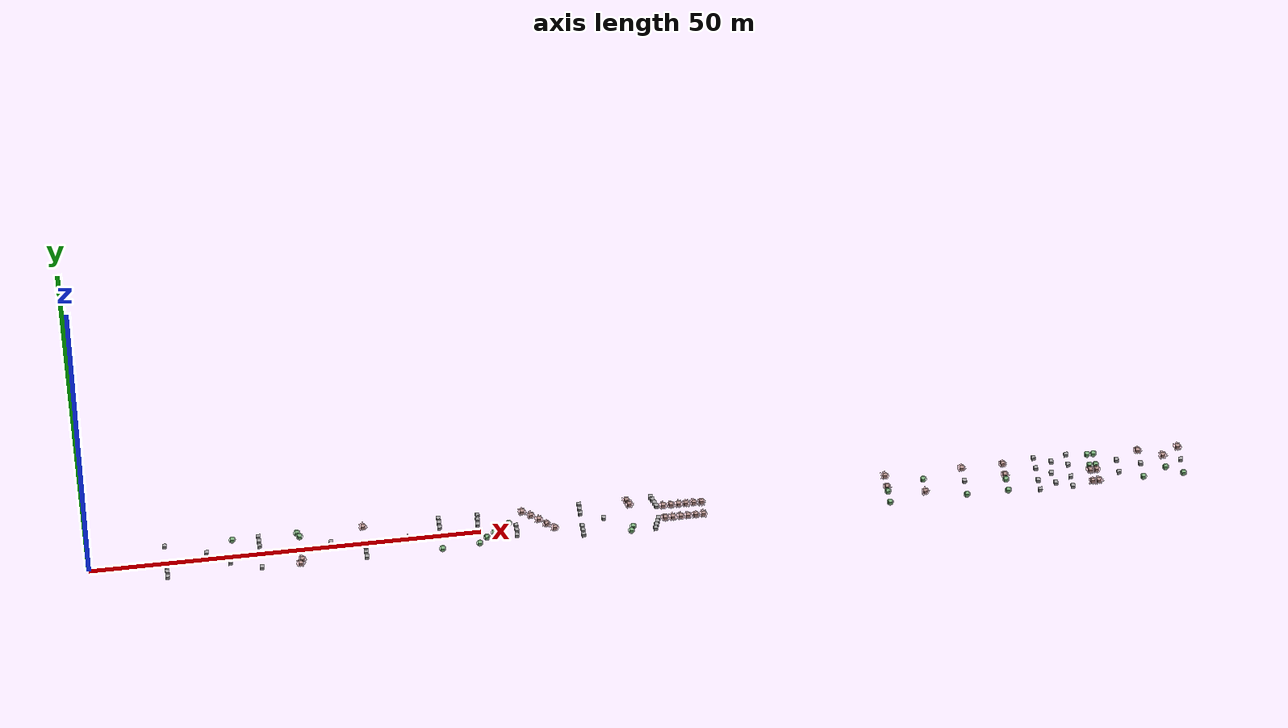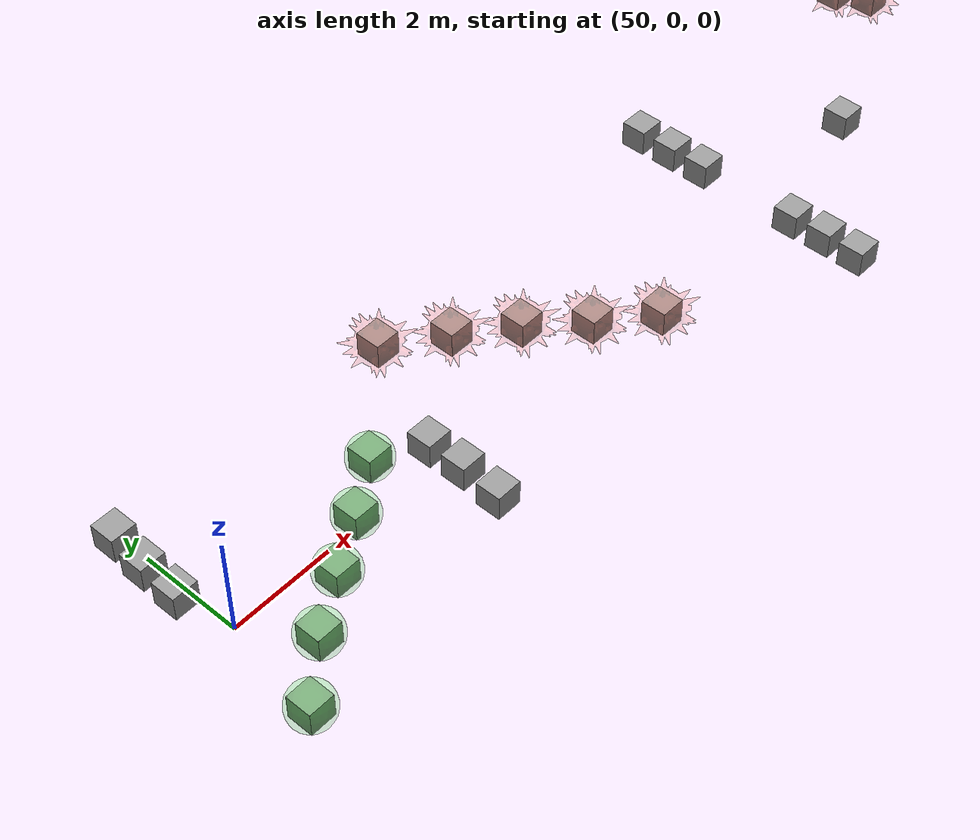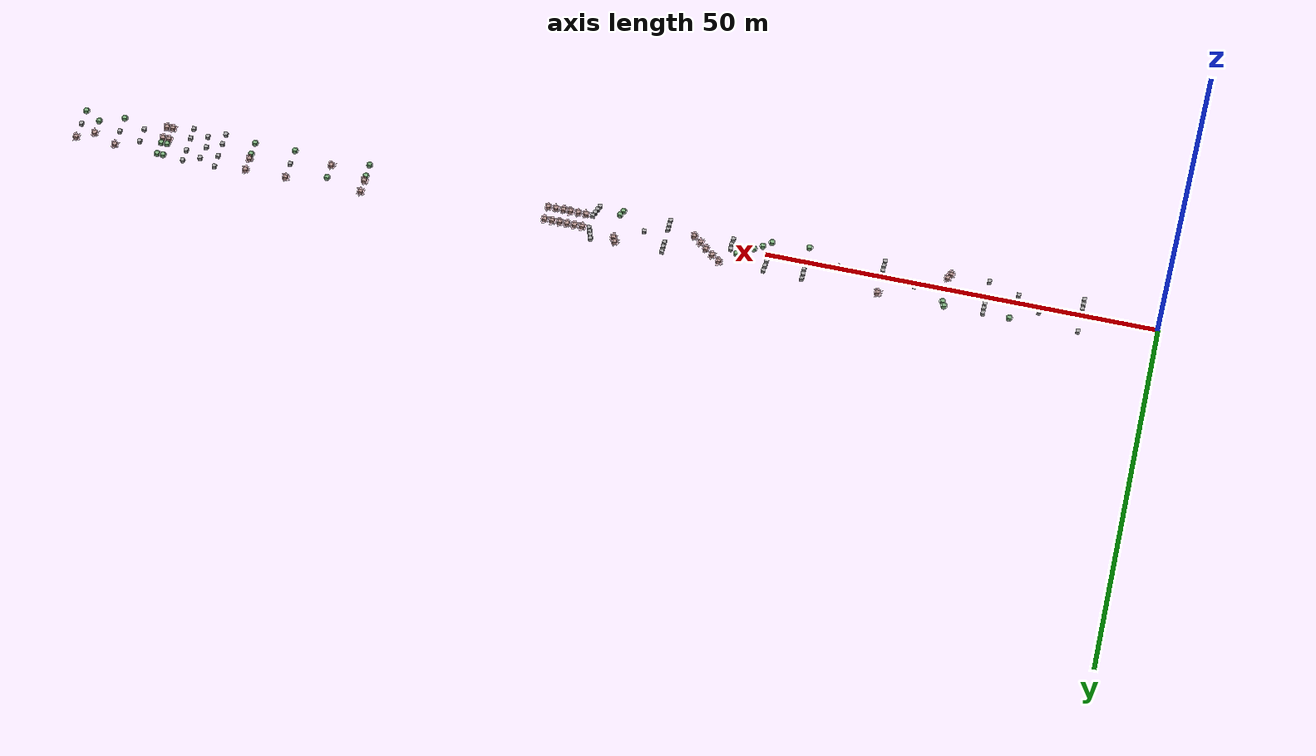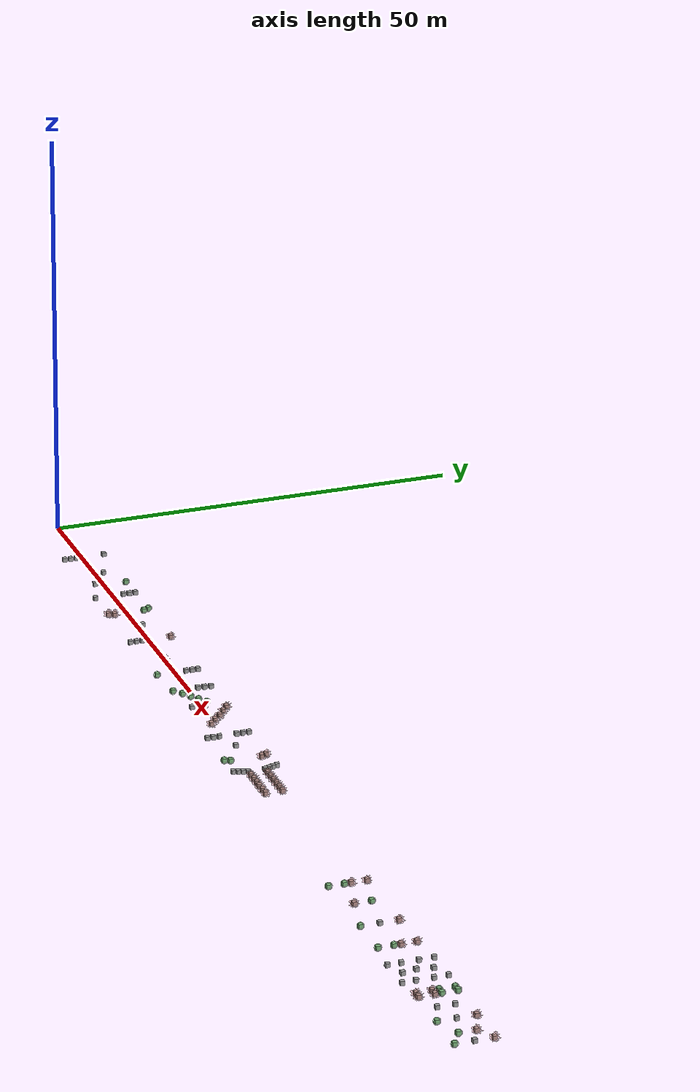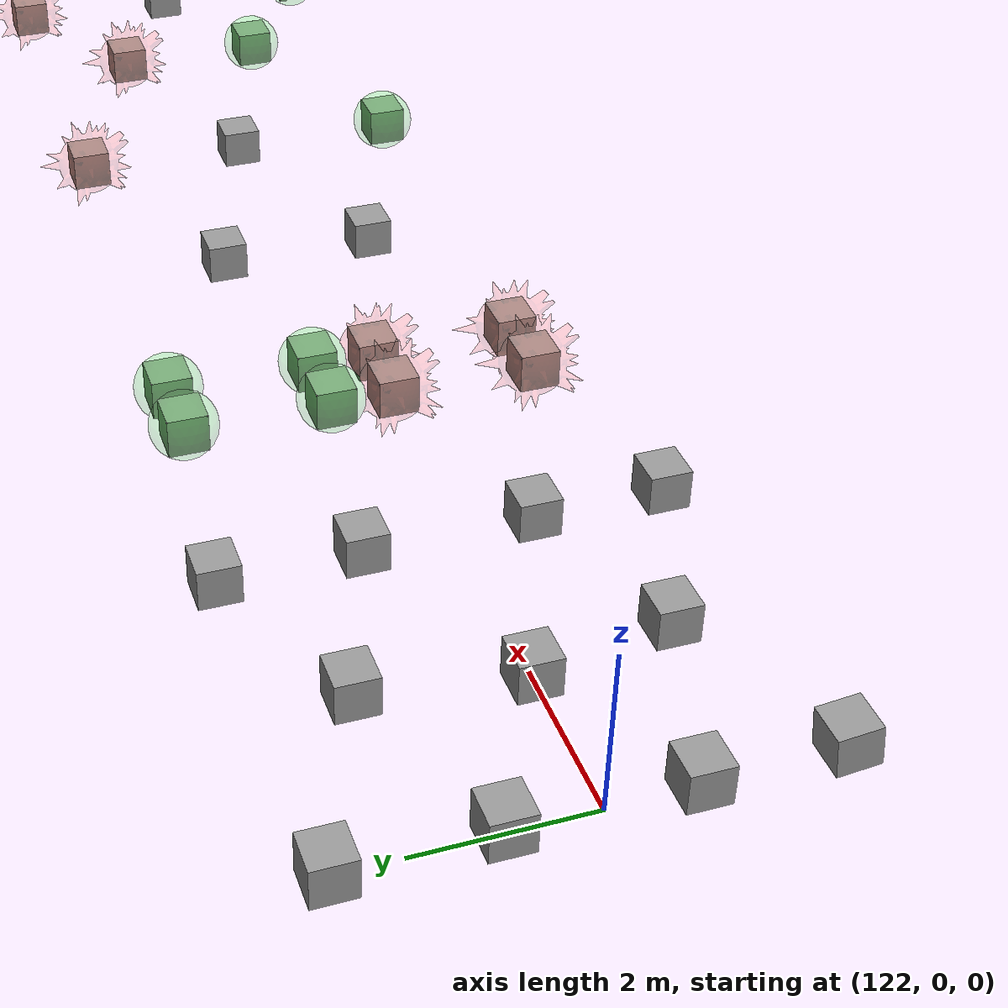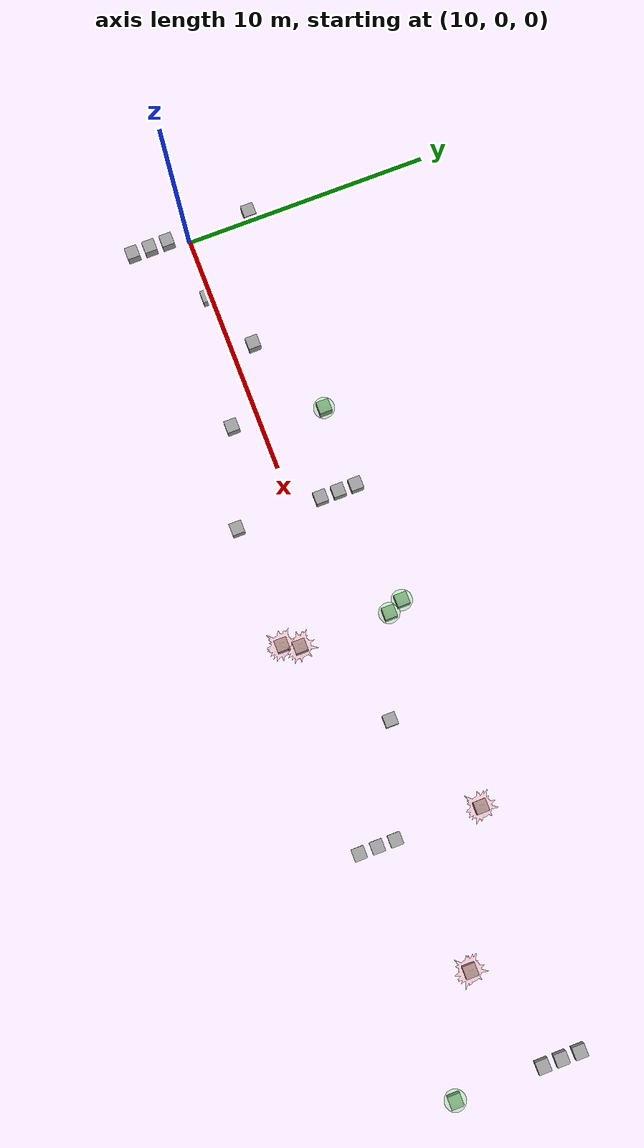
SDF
<sdf version="1.6">
 <world name="default">
  <light name="sun" type="directional">
   <pose>0 0 10 0 -0 0</pose>
   <diffuse>0.8 0.8 0.8 1</diffuse>
   <specular>0.2 0.2 0.2 1</specular>
   <attenuation>
    <range>1000</range>
    <constant>0.9</constant>
    <linear>0.01</linear>
    <quadratic>0.001</quadratic>
   </attenuation>
   <direction>-0.5 0.1 -0.9</direction>
  </light>
  <gravity>0 0 -9.8</gravity>
  <magnetic_field>6e-06 2.3e-05 -4.2e-05</magnetic_field>
  <atmosphere type="adiabatic"/>
  <physics name="default_physics" default="0" type="ode">
   <max_step_size>0.001</max_step_size>
   <real_time_factor>1</real_time_factor>
   <real_time_update_rate>1000</real_time_update_rate>
  </physics>
  <scene><ambient>0.4 0.4 0.4 1</ambient><background>0.9 0.9 0.9 1</background><shadows>1</shadows></scene>
  <spherical_coordinates>
   <surface_model>EARTH_WGS84</surface_model>
   <latitude_deg>0</latitude_deg>
   <longitude_deg>0</longitude_deg>
   <elevation>0</elevation>
   <heading_deg>0</heading_deg>
  </spherical_coordinates>
  <model name="trap_cont_1_attr">
   <static>0</static>
   <static>0</static>
   <link name="normal_cue_0::vis_cue_normal">
    <inertial>
     <mass>1</mass>
     <inertia>
      <ixx>0.166667</ixx>
      <ixy>0</ixy>
      <ixz>0</ixz>
      <iyy>0.166667</iyy>
      <iyz>0</iyz>
      <izz>0.166667</izz>
     </inertia>
    </inertial>
    <collision name="collision"><geometry><box><size>0.5 0.5 0.5</size></box></geometry></collision>
    <visual name="box_visual">
     <geometry><box><size>0.5 0.5 0.5</size></box></geometry>
     <material>
      <script><name>Gazebo/Grey</name><uri>file://media/materials/scripts/gazebo.material</uri></script>
     </material>
    </visual>
    <pose>0 -2.48 0.25 0 -0 0</pose>
   </link>
   <static>0</static>
   <link name="normal_cue_1::vis_cue_normal">
    <inertial>
     <mass>1</mass>
     <inertia>
      <ixx>0.166667</ixx>
      <ixy>0</ixy>
      <ixz>0</ixz>
      <iyy>0.166667</iyy>
      <iyz>0</iyz>
      <izz>0.166667</izz>
     </inertia>
    </inertial>
    <collision name="collision"><geometry><box><size>0.5 0.5 0.5</size></box></geometry></collision>
    <visual name="box_visual">
     <geometry><box><size>0.5 0.5 0.5</size></box></geometry>
     <material>
      <script><name>Gazebo/Grey</name><uri>file://media/materials/scripts/gazebo.material</uri></script>
     </material>
    </visual>
    <pose>0 -1.745 0.25 0 -0 0</pose>
   </link>
   <static>0</static>
   <link name="normal_cue_2::vis_cue_normal">
    <inertial>
     <mass>1</mass>
     <inertia>
      <ixx>0.166667</ixx>
      <ixy>0</ixy>
      <ixz>0</ixz>
      <iyy>0.166667</iyy>
      <iyz>0</iyz>
      <izz>0.166667</izz>
     </inertia>
    </inertial>
    <collision name="collision"><geometry><box><size>0.5 0.5 0.5</size></box></geometry></collision>
    <visual name="box_visual">
     <geometry><box><size>0.5 0.5 0.5</size></box></geometry>
     <material>
      <script><name>Gazebo/Grey</name><uri>file://media/materials/scripts/gazebo.material</uri></script>
     </material>
    </visual>
    <pose>0 -1.01 0.25 0 -0 0</pose>
   </link>
   <static>0</static>
   <link name="normal_cue_3::vis_cue_normal">
    <inertial>
     <mass>1</mass>
     <inertia>
      <ixx>0.166667</ixx>
      <ixy>0</ixy>
      <ixz>0</ixz>
      <iyy>0.166667</iyy>
      <iyz>0</iyz>
      <izz>0.166667</izz>
     </inertia>
    </inertial>
    <collision name="collision"><geometry><box><size>0.5 0.5 0.5</size></box></geometry></collision>
    <visual name="box_visual">
     <geometry><box><size>0.5 0.5 0.5</size></box></geometry>
     <material>
      <script><name>Gazebo/Grey</name><uri>file://media/materials/scripts/gazebo.material</uri></script>
     </material>
    </visual>
    <pose>0 2.48 0.25 0 -0 0</pose>
   </link>
   <pose>9.74623 0.150061 8e-06 6e-06 -6e-06 0</pose>
  </model>
  <model name="vis_cue_normal">
   <static>0</static>
   <pose>12.5084 -0.130294 0.249996 -7e-06 7e-06 0</pose>
   <link name="vis_cue_normal">
    <inertial>
     <mass>1</mass>
     <inertia>
      <ixx>0.166667</ixx>
      <ixy>0</ixy>
      <ixz>0</ixz>
      <iyy>0.166667</iyy>
      <iyz>0</iyz>
      <izz>0.166667</izz>
     </inertia>
    </inertial>
    <collision name="collision"><geometry><box><size>0.5 0.5 0.5</size></box></geometry></collision>
    <visual name="box_visual">
     <geometry><box><size>0.5 0.5 0.5</size></box></geometry>
     <material>
      <script><name>Gazebo/Grey</name><uri>file://media/materials/scripts/gazebo.material</uri></script>
     </material>
    </visual>
   </link>
  </model>
  <model name="vis_cue_normal_0">
   <static>0</static>
   <pose>14.9624 0.882672 0.249993 6e-06 -6e-06 0</pose>
   <link name="vis_cue_normal">
    <inertial>
     <mass>1</mass>
     <inertia>
      <ixx>0.166667</ixx>
      <ixy>0</ixy>
      <ixz>0</ixz>
      <iyy>0.166667</iyy>
      <iyz>0</iyz>
      <izz>0.166667</izz>
     </inertia>
    </inertial>
    <collision name="collision"><geometry><box><size>0.5 0.5 0.5</size></box></geometry></collision>
    <visual name="box_visual">
     <geometry><box><size>0.5 0.5 0.5</size></box></geometry>
     <material>
      <script><name>Gazebo/Grey</name><uri>file://media/materials/scripts/gazebo.material</uri></script>
     </material>
    </visual>
   </link>
  </model>
  <model name="vis_cue_normal_1">
   <static>0</static>
   <pose>17.8585 -1.08627 0.249993 0 6e-06 0</pose>
   <link name="vis_cue_normal">
    <inertial>
     <mass>1</mass>
     <inertia>
      <ixx>0.166667</ixx>
      <ixy>0</ixy>
      <ixz>0</ixz>
      <iyy>0.166667</iyy>
      <iyz>0</iyz>
      <izz>0.166667</izz>
     </inertia>
    </inertial>
    <collision name="collision"><geometry><box><size>0.5 0.5 0.5</size></box></geometry></collision>
    <visual name="box_visual">
     <geometry><box><size>0.5 0.5 0.5</size></box></geometry>
     <material>
      <script><name>Gazebo/Grey</name><uri>file://media/materials/scripts/gazebo.material</uri></script>
     </material>
    </visual>
   </link>
  </model>
  <model name="vis_cue_normal_2">
   <static>0</static>
   <pose>30.8778 0.555841 0.249997 0 -6e-06 0</pose>
   <link name="vis_cue_normal">
    <inertial>
     <mass>1</mass>
     <inertia>
      <ixx>0.166667</ixx>
      <ixy>0</ixy>
      <ixz>0</ixz>
      <iyy>0.166667</iyy>
      <iyz>0</iyz>
      <izz>0.166667</izz>
     </inertia>
    </inertial>
    <collision name="collision"><geometry><box><size>0.5 0.5 0.5</size></box></geometry></collision>
    <visual name="box_visual">
     <geometry><box><size>0.5 0.5 0.5</size></box></geometry>
     <material>
      <script><name>Gazebo/Grey</name><uri>file://media/materials/scripts/gazebo.material</uri></script>
     </material>
    </visual>
   </link>
  </model>
  <model name="trap_cont_1_repel">
   <static>0</static>
   <static>0</static>
   <link name="normal_cue_0::vis_cue_normal">
    <inertial>
     <mass>1</mass>
     <inertia>
      <ixx>0.166667</ixx>
      <ixy>0</ixy>
      <ixz>0</ixz>
      <iyy>0.166667</iyy>
      <iyz>0</iyz>
      <izz>0.166667</izz>
     </inertia>
    </inertial>
    <collision name="collision"><geometry><box><size>0.5 0.5 0.5</size></box></geometry></collision>
    <visual name="box_visual">
     <geometry><box><size>0.5 0.5 0.5</size></box></geometry>
     <material>
      <script><name>Gazebo/Grey</name><uri>file://media/materials/scripts/gazebo.material</uri></script>
     </material>
    </visual>
    <pose>0 -2.48 0.25 0 -0 0</pose>
   </link>
   <static>0</static>
   <link name="normal_cue_1::vis_cue_normal">
    <inertial>
     <mass>1</mass>
     <inertia>
      <ixx>0.166667</ixx>
      <ixy>0</ixy>
      <ixz>0</ixz>
      <iyy>0.166667</iyy>
      <iyz>0</iyz>
      <izz>0.166667</izz>
     </inertia>
    </inertial>
    <collision name="collision"><geometry><box><size>0.5 0.5 0.5</size></box></geometry></collision>
    <visual name="box_visual">
     <geometry><box><size>0.5 0.5 0.5</size></box></geometry>
     <material>
      <script><name>Gazebo/Grey</name><uri>file://media/materials/scripts/gazebo.material</uri></script>
     </material>
    </visual>
    <pose>0 1.01 0.25 0 -0 0</pose>
   </link>
   <static>0</static>
   <link name="normal_cue_2::vis_cue_normal">
    <inertial>
     <mass>1</mass>
     <inertia>
      <ixx>0.166667</ixx>
      <ixy>0</ixy>
      <ixz>0</ixz>
      <iyy>0.166667</iyy>
      <iyz>0</iyz>
      <izz>0.166667</izz>
     </inertia>
    </inertial>
    <collision name="collision"><geometry><box><size>0.5 0.5 0.5</size></box></geometry></collision>
    <visual name="box_visual">
     <geometry><box><size>0.5 0.5 0.5</size></box></geometry>
     <material>
      <script><name>Gazebo/Grey</name><uri>file://media/materials/scripts/gazebo.material</uri></script>
     </material>
    </visual>
    <pose>0 1.745 0.25 0 -0 0</pose>
   </link>
   <static>0</static>
   <link name="normal_cue_3::vis_cue_normal">
    <inertial>
     <mass>1</mass>
     <inertia>
      <ixx>0.166667</ixx>
      <ixy>0</ixy>
      <ixz>0</ixz>
      <iyy>0.166667</iyy>
      <iyz>0</iyz>
      <izz>0.166667</izz>
     </inertia>
    </inertial>
    <collision name="collision"><geometry><box><size>0.5 0.5 0.5</size></box></geometry></collision>
    <visual name="box_visual">
     <geometry><box><size>0.5 0.5 0.5</size></box></geometry>
     <material>
      <script><name>Gazebo/Grey</name><uri>file://media/materials/scripts/gazebo.material</uri></script>
     </material>
    </visual>
    <pose>0 2.48 0.25 0 -0 0</pose>
   </link>
   <pose>21.7795 0.155011 8e-06 6e-06 -6e-06 0</pose>
  </model>
  <model name="vis_cue_attract">
   <static>0</static>
   <pose>18.428 2.58126 0.249993 6e-06 -6e-06 0</pose>
   <link name="vis_cue_attract">
    <inertial>
     <mass>1</mass>
     <inertia>
      <ixx>0.166667</ixx>
      <ixy>0</ixy>
      <ixz>0</ixz>
      <iyy>0.166667</iyy>
      <iyz>0</iyz>
      <izz>0.166667</izz>
     </inertia>
    </inertial>
    <collision name="collision"><geometry><box><size>0.5 0.5 0.5</size></box></geometry></collision>
    <visual name="box_visual">
     <geometry><box><size>0.5 0.5 0.5</size></box></geometry>
     <material>
      <script><name>Gazebo/Grey</name><uri>file://media/materials/scripts/gazebo.material</uri></script>
     </material>
    </visual>
    <visual name="cue_visual">
     <geometry>
      <mesh><uri>model://vis_cue_attract/meshes/sphere.stl</uri><scale>0.85 0.85 0.85</scale></mesh>
     </geometry>
     <material>
      <ambient>0 1 0 0.15</ambient>
      <diffuse>0 1 0 0.15</diffuse>
      <specular>0 1 0 0.15</specular>
      <emissive>0 0 0 0</emissive>
     </material>
    </visual>
   </link>
  </model>
  <model name="trap_cont_2_ubias_m">
   <static>0</static>
   <static>0</static>
   <link name="repelling_cue_0::vis_cue_repel">
    <inertial>
     <mass>1</mass>
     <inertia>
      <ixx>0.166667</ixx>
      <ixy>0</ixy>
      <ixz>0</ixz>
      <iyy>0.166667</iyy>
      <iyz>0</iyz>
      <izz>0.166667</izz>
     </inertia>
    </inertial>
    <collision name="collision"><geometry><box><size>0.5 0.5 0.5</size></box></geometry></collision>
    <visual name="box_visual">
     <geometry><box><size>0.5 0.5 0.5</size></box></geometry>
     <material>
      <script><name>Gazebo/Grey</name><uri>file://media/materials/scripts/gazebo.material</uri></script>
     </material>
    </visual>
    <visual name="cue_visual">
     <geometry><mesh><uri>model://repelling_cue_2.dae</uri><scale>0.85 0.85 0.85</scale></mesh></geometry>
     <material>
      <ambient>1 0.3 0.2 0.2</ambient>
      <diffuse>1 0.3 0.2 0.2</diffuse>
      <specular>1 0.3 0.2 0.5</specular>
      <emissive>0.5 0 0 0.1</emissive>
     </material>
    </visual>
    <pose>0 -2.48 0.25 0 -0 0</pose>
   </link>
   <static>0</static>
   <link name="repelling_cue_1::vis_cue_repel">
    <inertial>
     <mass>1</mass>
     <inertia>
      <ixx>0.166667</ixx>
      <ixy>0</ixy>
      <ixz>0</ixz>
      <iyy>0.166667</iyy>
      <iyz>0</iyz>
      <izz>0.166667</izz>
     </inertia>
    </inertial>
    <collision name="collision"><geometry><box><size>0.5 0.5 0.5</size></box></geometry></collision>
    <visual name="box_visual">
     <geometry><box><size>0.5 0.5 0.5</size></box></geometry>
     <material>
      <script><name>Gazebo/Grey</name><uri>file://media/materials/scripts/gazebo.material</uri></script>
     </material>
    </visual>
    <visual name="cue_visual">
     <geometry><mesh><uri>model://repelling_cue_2.dae</uri><scale>0.85 0.85 0.85</scale></mesh></geometry>
     <material>
      <ambient>1 0.3 0.2 0.2</ambient>
      <diffuse>1 0.3 0.2 0.2</diffuse>
      <specular>1 0.3 0.2 0.5</specular>
      <emissive>0.5 0 0 0.1</emissive>
     </material>
    </visual>
    <pose>0.3 -1.845 0.25 0 -0 0</pose>
   </link>
   <static>0</static>
   <link name="attracting_cue_0::vis_cue_attract">
    <inertial>
     <mass>1</mass>
     <inertia>
      <ixx>0.166667</ixx>
      <ixy>0</ixy>
      <ixz>0</ixz>
      <iyy>0.166667</iyy>
      <iyz>0</iyz>
      <izz>0.166667</izz>
     </inertia>
    </inertial>
    <collision name="collision"><geometry><box><size>0.5 0.5 0.5</size></box></geometry></collision>
    <visual name="box_visual">
     <geometry><box><size>0.5 0.5 0.5</size></box></geometry>
     <material>
      <script><name>Gazebo/Grey</name><uri>file://media/materials/scripts/gazebo.material</uri></script>
     </material>
    </visual>
    <visual name="cue_visual">
     <geometry>
      <mesh><uri>model://vis_cue_attract/meshes/sphere.stl</uri><scale>0.85 0.85 0.85</scale></mesh>
     </geometry>
     <material>
      <ambient>0 1 0 0.15</ambient>
      <diffuse>0 1 0 0.15</diffuse>
      <specular>0 1 0 0.15</specular>
      <emissive>0 0 0 0</emissive>
     </material>
    </visual>
    <pose>0.3 1.845 0.25 0 -0 0</pose>
   </link>
   <static>0</static>
   <link name="attracting_cue_1::vis_cue_attract">
    <inertial>
     <mass>1</mass>
     <inertia>
      <ixx>0.166667</ixx>
      <ixy>0</ixy>
      <ixz>0</ixz>
      <iyy>0.166667</iyy>
      <iyz>0</iyz>
      <izz>0.166667</izz>
     </inertia>
    </inertial>
    <collision name="collision"><geometry><box><size>0.5 0.5 0.5</size></box></geometry></collision>
    <visual name="box_visual">
     <geometry><box><size>0.5 0.5 0.5</size></box></geometry>
     <material>
      <script><name>Gazebo/Grey</name><uri>file://media/materials/scripts/gazebo.material</uri></script>
     </material>
    </visual>
    <visual name="cue_visual">
     <geometry>
      <mesh><uri>model://vis_cue_attract/meshes/sphere.stl</uri><scale>0.85 0.85 0.85</scale></mesh>
     </geometry>
     <material>
      <ambient>0 1 0 0.15</ambient>
      <diffuse>0 1 0 0.15</diffuse>
      <specular>0 1 0 0.15</specular>
      <emissive>0 0 0 0</emissive>
     </material>
    </visual>
    <pose>0 2.48 0.25 0 -0 0</pose>
   </link>
   <pose>26.6934 0.180788 -2.1e-05 -7e-06 7e-06 0</pose>
  </model>
  <model name="trap_cont_1_repel_0">
   <static>0</static>
   <static>0</static>
   <link name="normal_cue_0::vis_cue_normal">
    <inertial>
     <mass>1</mass>
     <inertia>
      <ixx>0.166667</ixx>
      <ixy>0</ixy>
      <ixz>0</ixz>
      <iyy>0.166667</iyy>
      <iyz>0</iyz>
      <izz>0.166667</izz>
     </inertia>
    </inertial>
    <collision name="collision"><geometry><box><size>0.5 0.5 0.5</size></box></geometry></collision>
    <visual name="box_visual">
     <geometry><box><size>0.5 0.5 0.5</size></box></geometry>
     <material>
      <script><name>Gazebo/Grey</name><uri>file://media/materials/scripts/gazebo.material</uri></script>
     </material>
    </visual>
    <pose>0 -2.48 0.25 0 -0 0</pose>
   </link>
   <static>0</static>
   <link name="normal_cue_1::vis_cue_normal">
    <inertial>
     <mass>1</mass>
     <inertia>
      <ixx>0.166667</ixx>
      <ixy>0</ixy>
      <ixz>0</ixz>
      <iyy>0.166667</iyy>
      <iyz>0</iyz>
      <izz>0.166667</izz>
     </inertia>
    </inertial>
    <collision name="collision"><geometry><box><size>0.5 0.5 0.5</size></box></geometry></collision>
    <visual name="box_visual">
     <geometry><box><size>0.5 0.5 0.5</size></box></geometry>
     <material>
      <script><name>Gazebo/Grey</name><uri>file://media/materials/scripts/gazebo.material</uri></script>
     </material>
    </visual>
    <pose>0 -1.745 0.25 0 -0 0</pose>
   </link>
   <static>0</static>
   <link name="normal_cue_2::vis_cue_normal">
    <inertial>
     <mass>1</mass>
     <inertia>
      <ixx>0.166667</ixx>
      <ixy>0</ixy>
      <ixz>0</ixz>
      <iyy>0.166667</iyy>
      <iyz>0</iyz>
      <izz>0.166667</izz>
     </inertia>
    </inertial>
    <collision name="collision"><geometry><box><size>0.5 0.5 0.5</size></box></geometry></collision>
    <visual name="box_visual">
     <geometry><box><size>0.5 0.5 0.5</size></box></geometry>
     <material>
      <script><name>Gazebo/Grey</name><uri>file://media/materials/scripts/gazebo.material</uri></script>
     </material>
    </visual>
    <pose>0 -1.01 0.25 0 -0 0</pose>
   </link>
   <static>0</static>
   <link name="repelling_cue_0::vis_cue_repel">
    <inertial>
     <mass>1</mass>
     <inertia>
      <ixx>0.166667</ixx>
      <ixy>0</ixy>
      <ixz>0</ixz>
      <iyy>0.166667</iyy>
      <iyz>0</iyz>
      <izz>0.166667</izz>
     </inertia>
    </inertial>
    <collision name="collision"><geometry><box><size>0.5 0.5 0.5</size></box></geometry></collision>
    <visual name="box_visual">
     <geometry><box><size>0.5 0.5 0.5</size></box></geometry>
     <material>
      <script><name>Gazebo/Grey</name><uri>file://media/materials/scripts/gazebo.material</uri></script>
     </material>
    </visual>
    <visual name="cue_visual">
     <geometry><mesh><uri>model://repelling_cue_2.dae</uri><scale>0.85 0.85 0.85</scale></mesh></geometry>
     <material>
      <ambient>1 0.3 0.2 0.2</ambient>
      <diffuse>1 0.3 0.2 0.2</diffuse>
      <specular>1 0.3 0.2 0.5</specular>
      <emissive>0.5 0 0 0.1</emissive>
     </material>
    </visual>
    <pose>0 2.48 0.25 0 -0 0</pose>
   </link>
   <pose>35.1833 0.109631 8e-06 6e-06 -6e-06 0</pose>
  </model>
  <model name="vis_cue_repel">
   <static>0</static>
   <pose>40.708 -0.041063 0.249993 -6e-06 0 0</pose>
   <link name="vis_cue_repel">
    <inertial>
     <mass>1</mass>
     <inertia>
      <ixx>0.166667</ixx>
      <ixy>0</ixy>
      <ixz>0</ixz>
      <iyy>0.166667</iyy>
      <iyz>0</iyz>
      <izz>0.166667</izz>
     </inertia>
    </inertial>
    <collision name="collision"><geometry><box><size>0.5 0.5 0.5</size></box></geometry></collision>
    <visual name="box_visual">
     <geometry><box><size>0.5 0.5 0.5</size></box></geometry>
     <material>
      <script><name>Gazebo/Grey</name><uri>file://media/materials/scripts/gazebo.material</uri></script>
     </material>
    </visual>
    <visual name="cue_visual">
     <geometry><mesh><uri>model://repelling_cue_2.dae</uri><scale>0.85 0.85 0.85</scale></mesh></geometry>
     <material>
      <ambient>1 0.3 0.2 0.2</ambient>
      <diffuse>1 0.3 0.2 0.2</diffuse>
      <specular>1 0.3 0.2 0.5</specular>
      <emissive>0.5 0 0 0.1</emissive>
     </material>
    </visual>
   </link>
  </model>
  <model name="trap_cont_1_attr_m">
   <static>0</static>
   <static>0</static>
   <link name="attracting_cue_0::vis_cue_attract">
    <inertial>
     <mass>1</mass>
     <inertia>
      <ixx>0.166667</ixx>
      <ixy>0</ixy>
      <ixz>0</ixz>
      <iyy>0.166667</iyy>
      <iyz>0</iyz>
      <izz>0.166667</izz>
     </inertia>
    </inertial>
    <collision name="collision"><geometry><box><size>0.5 0.5 0.5</size></box></geometry></collision>
    <visual name="box_visual">
     <geometry><box><size>0.5 0.5 0.5</size></box></geometry>
     <material>
      <script><name>Gazebo/Grey</name><uri>file://media/materials/scripts/gazebo.material</uri></script>
     </material>
    </visual>
    <visual name="cue_visual">
     <geometry>
      <mesh><uri>model://vis_cue_attract/meshes/sphere.stl</uri><scale>0.85 0.85 0.85</scale></mesh>
     </geometry>
     <material>
      <ambient>0 1 0 0.15</ambient>
      <diffuse>0 1 0 0.15</diffuse>
      <specular>0 1 0 0.15</specular>
      <emissive>0 0 0 0</emissive>
     </material>
    </visual>
    <pose>0 -2.48 0.25 0 -0 0</pose>
   </link>
   <static>0</static>
   <link name="normal_cue_0::vis_cue_normal">
    <inertial>
     <mass>1</mass>
     <inertia>
      <ixx>0.166667</ixx>
      <ixy>0</ixy>
      <ixz>0</ixz>
      <iyy>0.166667</iyy>
      <iyz>0</iyz>
      <izz>0.166667</izz>
     </inertia>
    </inertial>
    <collision name="collision"><geometry><box><size>0.5 0.5 0.5</size></box></geometry></collision>
    <visual name="box_visual">
     <geometry><box><size>0.5 0.5 0.5</size></box></geometry>
     <material>
      <script><name>Gazebo/Grey</name><uri>file://media/materials/scripts/gazebo.material</uri></script>
     </material>
    </visual>
    <pose>0 1.01 0.25 0 -0 0</pose>
   </link>
   <static>0</static>
   <link name="normal_cue_1::vis_cue_normal">
    <inertial>
     <mass>1</mass>
     <inertia>
      <ixx>0.166667</ixx>
      <ixy>0</ixy>
      <ixz>0</ixz>
      <iyy>0.166667</iyy>
      <iyz>0</iyz>
      <izz>0.166667</izz>
     </inertia>
    </inertial>
    <collision name="collision"><geometry><box><size>0.5 0.5 0.5</size></box></geometry></collision>
    <visual name="box_visual">
     <geometry><box><size>0.5 0.5 0.5</size></box></geometry>
     <material>
      <script><name>Gazebo/Grey</name><uri>file://media/materials/scripts/gazebo.material</uri></script>
     </material>
    </visual>
    <pose>0 1.745 0.25 0 -0 0</pose>
   </link>
   <static>0</static>
   <link name="normal_cue_2::vis_cue_normal">
    <inertial>
     <mass>1</mass>
     <inertia>
      <ixx>0.166667</ixx>
      <ixy>0</ixy>
      <ixz>0</ixz>
      <iyy>0.166667</iyy>
      <iyz>0</iyz>
      <izz>0.166667</izz>
     </inertia>
    </inertial>
    <collision name="collision"><geometry><box><size>0.5 0.5 0.5</size></box></geometry></collision>
    <visual name="box_visual">
     <geometry><box><size>0.5 0.5 0.5</size></box></geometry>
     <material>
      <script><name>Gazebo/Grey</name><uri>file://media/materials/scripts/gazebo.material</uri></script>
     </material>
    </visual>
    <pose>0 2.48 0.25 0 -0 0</pose>
   </link>
   <pose>44.8837 0.193338 -2.1e-05 -7e-06 7e-06 0</pose>
  </model>
  <model name="vis_cue_attract_0">
   <static>0</static>
   <pose>49.6831 -1.98903 0.249993 -6e-06 0 0</pose>
   <link name="vis_cue_attract">
    <inertial>
     <mass>1</mass>
     <inertia>
      <ixx>0.166667</ixx>
      <ixy>0</ixy>
      <ixz>0</ixz>
      <iyy>0.166667</iyy>
      <iyz>0</iyz>
      <izz>0.166667</izz>
     </inertia>
    </inertial>
    <collision name="collision"><geometry><box><size>0.5 0.5 0.5</size></box></geometry></collision>
    <visual name="box_visual">
     <geometry><box><size>0.5 0.5 0.5</size></box></geometry>
     <material>
      <script><name>Gazebo/Grey</name><uri>file://media/materials/scripts/gazebo.material</uri></script>
     </material>
    </visual>
    <visual name="cue_visual">
     <geometry>
      <mesh><uri>model://vis_cue_attract/meshes/sphere.stl</uri><scale>0.85 0.85 0.85</scale></mesh>
     </geometry>
     <material>
      <ambient>0 1 0 0.15</ambient>
      <diffuse>0 1 0 0.15</diffuse>
      <specular>0 1 0 0.15</specular>
      <emissive>0 0 0 0</emissive>
     </material>
    </visual>
   </link>
  </model>
  <model name="vis_cue_attract_1">
   <static>0</static>
   <pose>50.6868 -1.1483 0.249992 3e-06 -5e-06 0</pose>
   <link name="vis_cue_attract">
    <inertial>
     <mass>1</mass>
     <inertia>
      <ixx>0.166667</ixx>
      <ixy>0</ixy>
      <ixz>0</ixz>
      <iyy>0.166667</iyy>
      <iyz>0</iyz>
      <izz>0.166667</izz>
     </inertia>
    </inertial>
    <collision name="collision"><geometry><box><size>0.5 0.5 0.5</size></box></geometry></collision>
    <visual name="box_visual">
     <geometry><box><size>0.5 0.5 0.5</size></box></geometry>
     <material>
      <script><name>Gazebo/Grey</name><uri>file://media/materials/scripts/gazebo.material</uri></script>
     </material>
    </visual>
    <visual name="cue_visual">
     <geometry>
      <mesh><uri>model://vis_cue_attract/meshes/sphere.stl</uri><scale>0.85 0.85 0.85</scale></mesh>
     </geometry>
     <material>
      <ambient>0 1 0 0.15</ambient>
      <diffuse>0 1 0 0.15</diffuse>
      <specular>0 1 0 0.15</specular>
      <emissive>0 0 0 0</emissive>
     </material>
    </visual>
   </link>
  </model>
  <model name="vis_cue_attract_2">
   <static>0</static>
   <pose>51.7096 -0.504608 0.249996 -7e-06 7e-06 0</pose>
   <link name="vis_cue_attract">
    <inertial>
     <mass>1</mass>
     <inertia>
      <ixx>0.166667</ixx>
      <ixy>0</ixy>
      <ixz>0</ixz>
      <iyy>0.166667</iyy>
      <iyz>0</iyz>
      <izz>0.166667</izz>
     </inertia>
    </inertial>
    <collision name="collision"><geometry><box><size>0.5 0.5 0.5</size></box></geometry></collision>
    <visual name="box_visual">
     <geometry><box><size>0.5 0.5 0.5</size></box></geometry>
     <material>
      <script><name>Gazebo/Grey</name><uri>file://media/materials/scripts/gazebo.material</uri></script>
     </material>
    </visual>
    <visual name="cue_visual">
     <geometry>
      <mesh><uri>model://vis_cue_attract/meshes/sphere.stl</uri><scale>0.85 0.85 0.85</scale></mesh>
     </geometry>
     <material>
      <ambient>0 1 0 0.15</ambient>
      <diffuse>0 1 0 0.15</diffuse>
      <specular>0 1 0 0.15</specular>
      <emissive>0 0 0 0</emissive>
     </material>
    </visual>
   </link>
  </model>
  <model name="vis_cue_attract_3">
   <static>0</static>
   <pose>52.7114 0.079456 0.249994 7e-06 -7e-06 0</pose>
   <link name="vis_cue_attract">
    <inertial>
     <mass>1</mass>
     <inertia>
      <ixx>0.166667</ixx>
      <ixy>0</ixy>
      <ixz>0</ixz>
      <iyy>0.166667</iyy>
      <iyz>0</iyz>
      <izz>0.166667</izz>
     </inertia>
    </inertial>
    <collision name="collision"><geometry><box><size>0.5 0.5 0.5</size></box></geometry></collision>
    <visual name="box_visual">
     <geometry><box><size>0.5 0.5 0.5</size></box></geometry>
     <material>
      <script><name>Gazebo/Grey</name><uri>file://media/materials/scripts/gazebo.material</uri></script>
     </material>
    </visual>
    <visual name="cue_visual">
     <geometry>
      <mesh><uri>model://vis_cue_attract/meshes/sphere.stl</uri><scale>0.85 0.85 0.85</scale></mesh>
     </geometry>
     <material>
      <ambient>0 1 0 0.15</ambient>
      <diffuse>0 1 0 0.15</diffuse>
      <specular>0 1 0 0.15</specular>
      <emissive>0 0 0 0</emissive>
     </material>
    </visual>
   </link>
  </model>
  <model name="vis_cue_attract_4">
   <static>0</static>
   <pose>53.7028 0.744254 0.249996 -7e-06 7e-06 0</pose>
   <link name="vis_cue_attract">
    <inertial>
     <mass>1</mass>
     <inertia>
      <ixx>0.166667</ixx>
      <ixy>0</ixy>
      <ixz>0</ixz>
      <iyy>0.166667</iyy>
      <iyz>0</iyz>
      <izz>0.166667</izz>
     </inertia>
    </inertial>
    <collision name="collision"><geometry><box><size>0.5 0.5 0.5</size></box></geometry></collision>
    <visual name="box_visual">
     <geometry><box><size>0.5 0.5 0.5</size></box></geometry>
     <material>
      <script><name>Gazebo/Grey</name><uri>file://media/materials/scripts/gazebo.material</uri></script>
     </material>
    </visual>
    <visual name="cue_visual">
     <geometry>
      <mesh><uri>model://vis_cue_attract/meshes/sphere.stl</uri><scale>0.85 0.85 0.85</scale></mesh>
     </geometry>
     <material>
      <ambient>0 1 0 0.15</ambient>
      <diffuse>0 1 0 0.15</diffuse>
      <specular>0 1 0 0.15</specular>
      <emissive>0 0 0 0</emissive>
     </material>
    </visual>
   </link>
  </model>
  <model name="vis_cue_normal_3">
   <static>0</static>
   <pose>49.8728 2.57254 0.249993 6e-06 -6e-06 0</pose>
   <link name="vis_cue_normal">
    <inertial>
     <mass>1</mass>
     <inertia>
      <ixx>0.166667</ixx>
      <ixy>0</ixy>
      <ixz>0</ixz>
      <iyy>0.166667</iyy>
      <iyz>0</iyz>
      <izz>0.166667</izz>
     </inertia>
    </inertial>
    <collision name="collision"><geometry><box><size>0.5 0.5 0.5</size></box></geometry></collision>
    <visual name="box_visual">
     <geometry><box><size>0.5 0.5 0.5</size></box></geometry>
     <material>
      <script><name>Gazebo/Grey</name><uri>file://media/materials/scripts/gazebo.material</uri></script>
     </material>
    </visual>
   </link>
  </model>
  <model name="vis_cue_normal_4">
   <static>0</static>
   <pose>49.7937 1.80764 0.249996 -7e-06 7e-06 0</pose>
   <link name="vis_cue_normal">
    <inertial>
     <mass>1</mass>
     <inertia>
      <ixx>0.166667</ixx>
      <ixy>0</ixy>
      <ixz>0</ixz>
      <iyy>0.166667</iyy>
      <iyz>0</iyz>
      <izz>0.166667</izz>
     </inertia>
    </inertial>
    <collision name="collision"><geometry><box><size>0.5 0.5 0.5</size></box></geometry></collision>
    <visual name="box_visual">
     <geometry><box><size>0.5 0.5 0.5</size></box></geometry>
     <material>
      <script><name>Gazebo/Grey</name><uri>file://media/materials/scripts/gazebo.material</uri></script>
     </material>
    </visual>
   </link>
  </model>
  <model name="vis_cue_normal_5">
   <static>0</static>
   <pose>49.7576 1.02957 0.249993 6e-06 -6e-06 0</pose>
   <link name="vis_cue_normal">
    <inertial>
     <mass>1</mass>
     <inertia>
      <ixx>0.166667</ixx>
      <ixy>0</ixy>
      <ixz>0</ixz>
      <iyy>0.166667</iyy>
      <iyz>0</iyz>
      <izz>0.166667</izz>
     </inertia>
    </inertial>
    <collision name="collision"><geometry><box><size>0.5 0.5 0.5</size></box></geometry></collision>
    <visual name="box_visual">
     <geometry><box><size>0.5 0.5 0.5</size></box></geometry>
     <material>
      <script><name>Gazebo/Grey</name><uri>file://media/materials/scripts/gazebo.material</uri></script>
     </material>
    </visual>
   </link>
  </model>
  <model name="vis_cue_repel_0">
   <static>0</static>
   <pose>55.6326 2.44766 0.249993 6e-06 -6e-06 0</pose>
   <link name="vis_cue_repel">
    <inertial>
     <mass>1</mass>
     <inertia>
      <ixx>0.166667</ixx>
      <ixy>0</ixy>
      <ixz>0</ixz>
      <iyy>0.166667</iyy>
      <iyz>0</iyz>
      <izz>0.166667</izz>
     </inertia>
    </inertial>
    <collision name="collision"><geometry><box><size>0.5 0.5 0.5</size></box></geometry></collision>
    <visual name="box_visual">
     <geometry><box><size>0.5 0.5 0.5</size></box></geometry>
     <material>
      <script><name>Gazebo/Grey</name><uri>file://media/materials/scripts/gazebo.material</uri></script>
     </material>
    </visual>
    <visual name="cue_visual">
     <geometry><mesh><uri>model://repelling_cue_2.dae</uri><scale>0.85 0.85 0.85</scale></mesh></geometry>
     <material>
      <ambient>1 0.3 0.2 0.2</ambient>
      <diffuse>1 0.3 0.2 0.2</diffuse>
      <specular>1 0.3 0.2 0.5</specular>
      <emissive>0.5 0 0 0.1</emissive>
     </material>
    </visual>
   </link>
  </model>
  <model name="vis_cue_repel_1">
   <static>0</static>
   <pose>56.6679 1.69987 0.249992 -4e-06 4e-06 0</pose>
   <link name="vis_cue_repel">
    <inertial>
     <mass>1</mass>
     <inertia>
      <ixx>0.166667</ixx>
      <ixy>0</ixy>
      <ixz>0</ixz>
      <iyy>0.166667</iyy>
      <iyz>0</iyz>
      <izz>0.166667</izz>
     </inertia>
    </inertial>
    <collision name="collision"><geometry><box><size>0.5 0.5 0.5</size></box></geometry></collision>
    <visual name="box_visual">
     <geometry><box><size>0.5 0.5 0.5</size></box></geometry>
     <material>
      <script><name>Gazebo/Grey</name><uri>file://media/materials/scripts/gazebo.material</uri></script>
     </material>
    </visual>
    <visual name="cue_visual">
     <geometry><mesh><uri>model://repelling_cue_2.dae</uri><scale>0.85 0.85 0.85</scale></mesh></geometry>
     <material>
      <ambient>1 0.3 0.2 0.2</ambient>
      <diffuse>1 0.3 0.2 0.2</diffuse>
      <specular>1 0.3 0.2 0.5</specular>
      <emissive>0.5 0 0 0.1</emissive>
     </material>
    </visual>
   </link>
  </model>
  <model name="vis_cue_repel_2">
   <static>0</static>
   <pose>57.6352 0.94533 0.249992 4e-06 3e-06 -0</pose>
   <link name="vis_cue_repel">
    <inertial>
     <mass>1</mass>
     <inertia>
      <ixx>0.166667</ixx>
      <ixy>0</ixy>
      <ixz>0</ixz>
      <iyy>0.166667</iyy>
      <iyz>0</iyz>
      <izz>0.166667</izz>
     </inertia>
    </inertial>
    <collision name="collision"><geometry><box><size>0.5 0.5 0.5</size></box></geometry></collision>
    <visual name="box_visual">
     <geometry><box><size>0.5 0.5 0.5</size></box></geometry>
     <material>
      <script><name>Gazebo/Grey</name><uri>file://media/materials/scripts/gazebo.material</uri></script>
     </material>
    </visual>
    <visual name="cue_visual">
     <geometry><mesh><uri>model://repelling_cue_2.dae</uri><scale>0.85 0.85 0.85</scale></mesh></geometry>
     <material>
      <ambient>1 0.3 0.2 0.2</ambient>
      <diffuse>1 0.3 0.2 0.2</diffuse>
      <specular>1 0.3 0.2 0.5</specular>
      <emissive>0.5 0 0 0.1</emissive>
     </material>
    </visual>
   </link>
  </model>
  <model name="vis_cue_repel_3">
   <static>0</static>
   <pose>58.5128 0.092665 0.249993 -6e-06 6e-06 0</pose>
   <link name="vis_cue_repel">
    <inertial>
     <mass>1</mass>
     <inertia>
      <ixx>0.166667</ixx>
      <ixy>0</ixy>
      <ixz>0</ixz>
      <iyy>0.166667</iyy>
      <iyz>0</iyz>
      <izz>0.166667</izz>
     </inertia>
    </inertial>
    <collision name="collision"><geometry><box><size>0.5 0.5 0.5</size></box></geometry></collision>
    <visual name="box_visual">
     <geometry><box><size>0.5 0.5 0.5</size></box></geometry>
     <material>
      <script><name>Gazebo/Grey</name><uri>file://media/materials/scripts/gazebo.material</uri></script>
     </material>
    </visual>
    <visual name="cue_visual">
     <geometry><mesh><uri>model://repelling_cue_2.dae</uri><scale>0.85 0.85 0.85</scale></mesh></geometry>
     <material>
      <ambient>1 0.3 0.2 0.2</ambient>
      <diffuse>1 0.3 0.2 0.2</diffuse>
      <specular>1 0.3 0.2 0.5</specular>
      <emissive>0.5 0 0 0.1</emissive>
     </material>
    </visual>
   </link>
  </model>
  <model name="vis_cue_repel_4">
   <static>0</static>
   <pose>59.4747 -0.665958 0.249992 3e-06 -5e-06 0</pose>
   <link name="vis_cue_repel">
    <inertial>
     <mass>1</mass>
     <inertia>
      <ixx>0.166667</ixx>
      <ixy>0</ixy>
      <ixz>0</ixz>
      <iyy>0.166667</iyy>
      <iyz>0</iyz>
      <izz>0.166667</izz>
     </inertia>
    </inertial>
    <collision name="collision"><geometry><box><size>0.5 0.5 0.5</size></box></geometry></collision>
    <visual name="box_visual">
     <geometry><box><size>0.5 0.5 0.5</size></box></geometry>
     <material>
      <script><name>Gazebo/Grey</name><uri>file://media/materials/scripts/gazebo.material</uri></script>
     </material>
    </visual>
    <visual name="cue_visual">
     <geometry><mesh><uri>model://repelling_cue_2.dae</uri><scale>0.85 0.85 0.85</scale></mesh></geometry>
     <material>
      <ambient>1 0.3 0.2 0.2</ambient>
      <diffuse>1 0.3 0.2 0.2</diffuse>
      <specular>1 0.3 0.2 0.5</specular>
      <emissive>0.5 0 0 0.1</emissive>
     </material>
    </visual>
   </link>
  </model>
  <model name="vis_cue_normal_6">
   <static>0</static>
   <pose>54.5835 0.254387 0.249996 -7e-06 7e-06 0</pose>
   <link name="vis_cue_normal">
    <inertial>
     <mass>1</mass>
     <inertia>
      <ixx>0.166667</ixx>
      <ixy>0</ixy>
      <ixz>0</ixz>
      <iyy>0.166667</iyy>
      <iyz>0</iyz>
      <izz>0.166667</izz>
     </inertia>
    </inertial>
    <collision name="collision"><geometry><box><size>0.5 0.5 0.5</size></box></geometry></collision>
    <visual name="box_visual">
     <geometry><box><size>0.5 0.5 0.5</size></box></geometry>
     <material>
      <script><name>Gazebo/Grey</name><uri>file://media/materials/scripts/gazebo.material</uri></script>
     </material>
    </visual>
   </link>
  </model>
  <model name="vis_cue_normal_7">
   <static>0</static>
   <pose>54.5924 -0.485049 0.249993 6e-06 -6e-06 0</pose>
   <link name="vis_cue_normal">
    <inertial>
     <mass>1</mass>
     <inertia>
      <ixx>0.166667</ixx>
      <ixy>0</ixy>
      <ixz>0</ixz>
      <iyy>0.166667</iyy>
      <iyz>0</iyz>
      <izz>0.166667</izz>
     </inertia>
    </inertial>
    <collision name="collision"><geometry><box><size>0.5 0.5 0.5</size></box></geometry></collision>
    <visual name="box_visual">
     <geometry><box><size>0.5 0.5 0.5</size></box></geometry>
     <material>
      <script><name>Gazebo/Grey</name><uri>file://media/materials/scripts/gazebo.material</uri></script>
     </material>
    </visual>
   </link>
  </model>
  <model name="vis_cue_normal_8">
   <static>0</static>
   <pose>54.5258 -1.30491 0.249996 -7e-06 7e-06 0</pose>
   <link name="vis_cue_normal">
    <inertial>
     <mass>1</mass>
     <inertia>
      <ixx>0.166667</ixx>
      <ixy>0</ixy>
      <ixz>0</ixz>
      <iyy>0.166667</iyy>
      <iyz>0</iyz>
      <izz>0.166667</izz>
     </inertia>
    </inertial>
    <collision name="collision"><geometry><box><size>0.5 0.5 0.5</size></box></geometry></collision>
    <visual name="box_visual">
     <geometry><box><size>0.5 0.5 0.5</size></box></geometry>
     <material>
      <script><name>Gazebo/Grey</name><uri>file://media/materials/scripts/gazebo.material</uri></script>
     </material>
    </visual>
   </link>
  </model>
  <model name="trap_cont_1_repel_1">
   <static>0</static>
   <static>0</static>
   <link name="normal_cue_0::vis_cue_normal">
    <inertial>
     <mass>1</mass>
     <inertia>
      <ixx>0.166667</ixx>
      <ixy>0</ixy>
      <ixz>0</ixz>
      <iyy>0.166667</iyy>
      <iyz>0</iyz>
      <izz>0.166667</izz>
     </inertia>
    </inertial>
    <collision name="collision"><geometry><box><size>0.5 0.5 0.5</size></box></geometry></collision>
    <visual name="box_visual">
     <geometry><box><size>0.5 0.5 0.5</size></box></geometry>
     <material>
      <script><name>Gazebo/Grey</name><uri>file://media/materials/scripts/gazebo.material</uri></script>
     </material>
    </visual>
    <pose>0 -2.48 0.25 0 -0 0</pose>
   </link>
   <static>0</static>
   <link name="normal_cue_1::vis_cue_normal">
    <inertial>
     <mass>1</mass>
     <inertia>
      <ixx>0.166667</ixx>
      <ixy>0</ixy>
      <ixz>0</ixz>
      <iyy>0.166667</iyy>
      <iyz>0</iyz>
      <izz>0.166667</izz>
     </inertia>
    </inertial>
    <collision name="collision"><geometry><box><size>0.5 0.5 0.5</size></box></geometry></collision>
    <visual name="box_visual">
     <geometry><box><size>0.5 0.5 0.5</size></box></geometry>
     <material>
      <script><name>Gazebo/Grey</name><uri>file://media/materials/scripts/gazebo.material</uri></script>
     </material>
    </visual>
    <pose>0 1.01 0.25 0 -0 0</pose>
   </link>
   <static>0</static>
   <link name="normal_cue_2::vis_cue_normal">
    <inertial>
     <mass>1</mass>
     <inertia>
      <ixx>0.166667</ixx>
      <ixy>0</ixy>
      <ixz>0</ixz>
      <iyy>0.166667</iyy>
      <iyz>0</iyz>
      <izz>0.166667</izz>
     </inertia>
    </inertial>
    <collision name="collision"><geometry><box><size>0.5 0.5 0.5</size></box></geometry></collision>
    <visual name="box_visual">
     <geometry><box><size>0.5 0.5 0.5</size></box></geometry>
     <material>
      <script><name>Gazebo/Grey</name><uri>file://media/materials/scripts/gazebo.material</uri></script>
     </material>
    </visual>
    <pose>0 1.745 0.25 0 -0 0</pose>
   </link>
   <static>0</static>
   <link name="normal_cue_3::vis_cue_normal">
    <inertial>
     <mass>1</mass>
     <inertia>
      <ixx>0.166667</ixx>
      <ixy>0</ixy>
      <ixz>0</ixz>
      <iyy>0.166667</iyy>
      <iyz>0</iyz>
      <izz>0.166667</izz>
     </inertia>
    </inertial>
    <collision name="collision"><geometry><box><size>0.5 0.5 0.5</size></box></geometry></collision>
    <visual name="box_visual">
     <geometry><box><size>0.5 0.5 0.5</size></box></geometry>
     <material>
      <script><name>Gazebo/Grey</name><uri>file://media/materials/scripts/gazebo.material</uri></script>
     </material>
    </visual>
    <pose>0 2.48 0.25 0 -0 0</pose>
   </link>
   <pose>62.9652 0.149729 -1.8e-05 -6e-06 6e-06 0</pose>
  </model>
  <model name="trap_cont_2_ubias">
   <static>0</static>
   <static>0</static>
   <link name="attracting_cue_0::vis_cue_attract">
    <inertial>
     <mass>1</mass>
     <inertia>
      <ixx>0.166667</ixx>
      <ixy>0</ixy>
      <ixz>0</ixz>
      <iyy>0.166667</iyy>
      <iyz>0</iyz>
      <izz>0.166667</izz>
     </inertia>
    </inertial>
    <collision name="collision"><geometry><box><size>0.5 0.5 0.5</size></box></geometry></collision>
    <visual name="box_visual">
     <geometry><box><size>0.5 0.5 0.5</size></box></geometry>
     <material>
      <script><name>Gazebo/Grey</name><uri>file://media/materials/scripts/gazebo.material</uri></script>
     </material>
    </visual>
    <visual name="cue_visual">
     <geometry>
      <mesh><uri>model://vis_cue_attract/meshes/sphere.stl</uri><scale>0.85 0.85 0.85</scale></mesh>
     </geometry>
     <material>
      <ambient>0 1 0 0.15</ambient>
      <diffuse>0 1 0 0.15</diffuse>
      <specular>0 1 0 0.15</specular>
      <emissive>0 0 0 0</emissive>
     </material>
    </visual>
    <pose>0 -2.48 0.25 0 -0 0</pose>
   </link>
   <static>0</static>
   <link name="attracting_cue_1::vis_cue_attract">
    <inertial>
     <mass>1</mass>
     <inertia>
      <ixx>0.166667</ixx>
      <ixy>0</ixy>
      <ixz>0</ixz>
      <iyy>0.166667</iyy>
      <iyz>0</iyz>
      <izz>0.166667</izz>
     </inertia>
    </inertial>
    <collision name="collision"><geometry><box><size>0.5 0.5 0.5</size></box></geometry></collision>
    <visual name="box_visual">
     <geometry><box><size>0.5 0.5 0.5</size></box></geometry>
     <material>
      <script><name>Gazebo/Grey</name><uri>file://media/materials/scripts/gazebo.material</uri></script>
     </material>
    </visual>
    <visual name="cue_visual">
     <geometry>
      <mesh><uri>model://vis_cue_attract/meshes/sphere.stl</uri><scale>0.85 0.85 0.85</scale></mesh>
     </geometry>
     <material>
      <ambient>0 1 0 0.15</ambient>
      <diffuse>0 1 0 0.15</diffuse>
      <specular>0 1 0 0.15</specular>
      <emissive>0 0 0 0</emissive>
     </material>
    </visual>
    <pose>0.3 -1.845 0.25 0 -0 0</pose>
   </link>
   <static>0</static>
   <link name="repelling_cue_0::vis_cue_repel">
    <inertial>
     <mass>1</mass>
     <inertia>
      <ixx>0.166667</ixx>
      <ixy>0</ixy>
      <ixz>0</ixz>
      <iyy>0.166667</iyy>
      <iyz>0</iyz>
      <izz>0.166667</izz>
     </inertia>
    </inertial>
    <collision name="collision"><geometry><box><size>0.5 0.5 0.5</size></box></geometry></collision>
    <visual name="box_visual">
     <geometry><box><size>0.5 0.5 0.5</size></box></geometry>
     <material>
      <script><name>Gazebo/Grey</name><uri>file://media/materials/scripts/gazebo.material</uri></script>
     </material>
    </visual>
    <visual name="cue_visual">
     <geometry><mesh><uri>model://repelling_cue_2.dae</uri><scale>0.85 0.85 0.85</scale></mesh></geometry>
     <material>
      <ambient>1 0.3 0.2 0.2</ambient>
      <diffuse>1 0.3 0.2 0.2</diffuse>
      <specular>1 0.3 0.2 0.5</specular>
      <emissive>0.5 0 0 0.1</emissive>
     </material>
    </visual>
    <pose>0.3 1.845 0.25 0 -0 0</pose>
   </link>
   <static>0</static>
   <link name="repelling_cue_1::vis_cue_repel">
    <inertial>
     <mass>1</mass>
     <inertia>
      <ixx>0.166667</ixx>
      <ixy>0</ixy>
      <ixz>0</ixz>
      <iyy>0.166667</iyy>
      <iyz>0</iyz>
      <izz>0.166667</izz>
     </inertia>
    </inertial>
    <collision name="collision"><geometry><box><size>0.5 0.5 0.5</size></box></geometry></collision>
    <visual name="box_visual">
     <geometry><box><size>0.5 0.5 0.5</size></box></geometry>
     <material>
      <script><name>Gazebo/Grey</name><uri>file://media/materials/scripts/gazebo.material</uri></script>
     </material>
    </visual>
    <visual name="cue_visual">
     <geometry><mesh><uri>model://repelling_cue_2.dae</uri><scale>0.85 0.85 0.85</scale></mesh></geometry>
     <material>
      <ambient>1 0.3 0.2 0.2</ambient>
      <diffuse>1 0.3 0.2 0.2</diffuse>
      <specular>1 0.3 0.2 0.5</specular>
      <emissive>0.5 0 0 0.1</emissive>
     </material>
    </visual>
    <pose>0 2.48 0.25 0 -0 0</pose>
   </link>
   <pose>69.1149 0.054682 1.1e-05 7e-06 -7e-06 0</pose>
  </model>
  <model name="vis_cue_normal_9">
   <static>0</static>
   <pose>62.976 -1.62281 0.249994 7e-06 -7e-06 0</pose>
   <link name="vis_cue_normal">
    <inertial>
     <mass>1</mass>
     <inertia>
      <ixx>0.166667</ixx>
      <ixy>0</ixy>
      <ixz>0</ixz>
      <iyy>0.166667</iyy>
      <iyz>0</iyz>
      <izz>0.166667</izz>
     </inertia>
    </inertial>
    <collision name="collision"><geometry><box><size>0.5 0.5 0.5</size></box></geometry></collision>
    <visual name="box_visual">
     <geometry><box><size>0.5 0.5 0.5</size></box></geometry>
     <material>
      <script><name>Gazebo/Grey</name><uri>file://media/materials/scripts/gazebo.material</uri></script>
     </material>
    </visual>
   </link>
  </model>
  <model name="vis_cue_normal_10">
   <static>0</static>
   <pose>62.9647 -0.89842 0.249997 -6e-06 6e-06 0</pose>
   <link name="vis_cue_normal">
    <inertial>
     <mass>1</mass>
     <inertia>
      <ixx>0.166667</ixx>
      <ixy>0</ixy>
      <ixz>0</ixz>
      <iyy>0.166667</iyy>
      <iyz>0</iyz>
      <izz>0.166667</izz>
     </inertia>
    </inertial>
    <collision name="collision"><geometry><box><size>0.5 0.5 0.5</size></box></geometry></collision>
    <visual name="box_visual">
     <geometry><box><size>0.5 0.5 0.5</size></box></geometry>
     <material>
      <script><name>Gazebo/Grey</name><uri>file://media/materials/scripts/gazebo.material</uri></script>
     </material>
    </visual>
   </link>
  </model>
  <model name="vis_cue_normal_11">
   <static>0</static>
   <pose>65.8524 0.063118 0.249997 -6e-06 6e-06 0</pose>
   <link name="vis_cue_normal">
    <inertial>
     <mass>1</mass>
     <inertia>
      <ixx>0.166667</ixx>
      <ixy>0</ixy>
      <ixz>0</ixz>
      <iyy>0.166667</iyy>
      <iyz>0</iyz>
      <izz>0.166667</izz>
     </inertia>
    </inertial>
    <collision name="collision"><geometry><box><size>0.5 0.5 0.5</size></box></geometry></collision>
    <visual name="box_visual">
     <geometry><box><size>0.5 0.5 0.5</size></box></geometry>
     <material>
      <script><name>Gazebo/Grey</name><uri>file://media/materials/scripts/gazebo.material</uri></script>
     </material>
    </visual>
   </link>
  </model>
  <model name="trap_gate">
   <static>1</static>
   <static>0</static>
   <link name="normal_cue_0::vis_cue_normal">
    <inertial>
     <mass>1</mass>
     <inertia>
      <ixx>0.166667</ixx>
      <ixy>0</ixy>
      <ixz>0</ixz>
      <iyy>0.166667</iyy>
      <iyz>0</iyz>
      <izz>0.166667</izz>
     </inertia>
    </inertial>
    <collision name="collision"><geometry><box><size>0.5 0.5 0.5</size></box></geometry></collision>
    <visual name="box_visual">
     <geometry><box><size>0.5 0.5 0.5</size></box></geometry>
     <material>
      <script><name>Gazebo/Grey</name><uri>file://media/materials/scripts/gazebo.material</uri></script>
     </material>
    </visual>
    <pose>0 -2.6 0.25 0 -0 0</pose>
   </link>
   <static>0</static>
   <link name="normal_cue_1::vis_cue_normal">
    <inertial>
     <mass>1</mass>
     <inertia>
      <ixx>0.166667</ixx>
      <ixy>0</ixy>
      <ixz>0</ixz>
      <iyy>0.166667</iyy>
      <iyz>0</iyz>
      <izz>0.166667</izz>
     </inertia>
    </inertial>
    <collision name="collision"><geometry><box><size>0.5 0.5 0.5</size></box></geometry></collision>
    <visual name="box_visual">
     <geometry><box><size>0.5 0.5 0.5</size></box></geometry>
     <material>
      <script><name>Gazebo/Grey</name><uri>file://media/materials/scripts/gazebo.material</uri></script>
     </material>
    </visual>
    <pose>0.19 -2.06 0.25 0 -0 0</pose>
   </link>
   <static>0</static>
   <link name="normal_cue_2::vis_cue_normal">
    <inertial>
     <mass>1</mass>
     <inertia>
      <ixx>0.166667</ixx>
      <ixy>0</ixy>
      <ixz>0</ixz>
      <iyy>0.166667</iyy>
      <iyz>0</iyz>
      <izz>0.166667</izz>
     </inertia>
    </inertial>
    <collision name="collision"><geometry><box><size>0.5 0.5 0.5</size></box></geometry></collision>
    <visual name="box_visual">
     <geometry><box><size>0.5 0.5 0.5</size></box></geometry>
     <material>
      <script><name>Gazebo/Grey</name><uri>file://media/materials/scripts/gazebo.material</uri></script>
     </material>
    </visual>
    <pose>0.37 -1.53 0.25 0 -0 0</pose>
   </link>
   <static>0</static>
   <link name="normal_cue_3::vis_cue_normal">
    <inertial>
     <mass>1</mass>
     <inertia>
      <ixx>0.166667</ixx>
      <ixy>0</ixy>
      <ixz>0</ixz>
      <iyy>0.166667</iyy>
      <iyz>0</iyz>
      <izz>0.166667</izz>
     </inertia>
    </inertial>
    <collision name="collision"><geometry><box><size>0.5 0.5 0.5</size></box></geometry></collision>
    <visual name="box_visual">
     <geometry><box><size>0.5 0.5 0.5</size></box></geometry>
     <material>
      <script><name>Gazebo/Grey</name><uri>file://media/materials/scripts/gazebo.material</uri></script>
     </material>
    </visual>
    <pose>0.56 -1 0.25 0 -0 0</pose>
   </link>
   <static>0</static>
   <link name="normal_cue_4::vis_cue_normal">
    <inertial>
     <mass>1</mass>
     <inertia>
      <ixx>0.166667</ixx>
      <ixy>0</ixy>
      <ixz>0</ixz>
      <iyy>0.166667</iyy>
      <iyz>0</iyz>
      <izz>0.166667</izz>
     </inertia>
    </inertial>
    <collision name="collision"><geometry><box><size>0.5 0.5 0.5</size></box></geometry></collision>
    <visual name="box_visual">
     <geometry><box><size>0.5 0.5 0.5</size></box></geometry>
     <material>
      <script><name>Gazebo/Grey</name><uri>file://media/materials/scripts/gazebo.material</uri></script>
     </material>
    </visual>
    <pose>0.56 1 0.25 0 -0 0</pose>
   </link>
   <static>0</static>
   <link name="normal_cue_5::vis_cue_normal">
    <inertial>
     <mass>1</mass>
     <inertia>
      <ixx>0.166667</ixx>
      <ixy>0</ixy>
      <ixz>0</ixz>
      <iyy>0.166667</iyy>
      <iyz>0</iyz>
      <izz>0.166667</izz>
     </inertia>
    </inertial>
    <collision name="collision"><geometry><box><size>0.5 0.5 0.5</size></box></geometry></collision>
    <visual name="box_visual">
     <geometry><box><size>0.5 0.5 0.5</size></box></geometry>
     <material>
      <script><name>Gazebo/Grey</name><uri>file://media/materials/scripts/gazebo.material</uri></script>
     </material>
    </visual>
    <pose>0.37 1.53 0.25 0 -0 0</pose>
   </link>
   <static>0</static>
   <link name="normal_cue_6::vis_cue_normal">
    <inertial>
     <mass>1</mass>
     <inertia>
      <ixx>0.166667</ixx>
      <ixy>0</ixy>
      <ixz>0</ixz>
      <iyy>0.166667</iyy>
      <iyz>0</iyz>
      <izz>0.166667</izz>
     </inertia>
    </inertial>
    <collision name="collision"><geometry><box><size>0.5 0.5 0.5</size></box></geometry></collision>
    <visual name="box_visual">
     <geometry><box><size>0.5 0.5 0.5</size></box></geometry>
     <material>
      <script><name>Gazebo/Grey</name><uri>file://media/materials/scripts/gazebo.material</uri></script>
     </material>
    </visual>
    <pose>0.19 2.06 0.25 0 -0 0</pose>
   </link>
   <static>0</static>
   <link name="normal_cue_7::vis_cue_normal">
    <inertial>
     <mass>1</mass>
     <inertia>
      <ixx>0.166667</ixx>
      <ixy>0</ixy>
      <ixz>0</ixz>
      <iyy>0.166667</iyy>
      <iyz>0</iyz>
      <izz>0.166667</izz>
     </inertia>
    </inertial>
    <collision name="collision"><geometry><box><size>0.5 0.5 0.5</size></box></geometry></collision>
    <visual name="box_visual">
     <geometry><box><size>0.5 0.5 0.5</size></box></geometry>
     <material>
      <script><name>Gazebo/Grey</name><uri>file://media/materials/scripts/gazebo.material</uri></script>
     </material>
    </visual>
    <pose>0 2.6 0.25 0 -0 0</pose>
   </link>
   <pose>72.2127 0.15245 0 0 -0 0</pose>
  </model>
  <model name="trap_discr_2_ubias">
   <static>0</static>
   <static>0</static>
   <link name="attract_cue_0::vis_cue_attract">
    <inertial>
     <mass>1</mass>
     <inertia>
      <ixx>0.166667</ixx>
      <ixy>0</ixy>
      <ixz>0</ixz>
      <iyy>0.166667</iyy>
      <iyz>0</iyz>
      <izz>0.166667</izz>
     </inertia>
    </inertial>
    <collision name="collision"><geometry><box><size>0.5 0.5 0.5</size></box></geometry></collision>
    <visual name="box_visual">
     <geometry><box><size>0.5 0.5 0.5</size></box></geometry>
     <material>
      <script><name>Gazebo/Grey</name><uri>file://media/materials/scripts/gazebo.material</uri></script>
     </material>
    </visual>
    <visual name="cue_visual">
     <geometry>
      <mesh><uri>model://vis_cue_attract/meshes/sphere.stl</uri><scale>0.85 0.85 0.85</scale></mesh>
     </geometry>
     <material>
      <ambient>0 1 0 0.15</ambient>
      <diffuse>0 1 0 0.15</diffuse>
      <specular>0 1 0 0.15</specular>
      <emissive>0 0 0 0</emissive>
     </material>
    </visual>
    <pose>0 -2.2 0.25 0 -0 0</pose>
   </link>
   <static>0</static>
   <link name="attract_cue_1::vis_cue_attract">
    <inertial>
     <mass>1</mass>
     <inertia>
      <ixx>0.166667</ixx>
      <ixy>0</ixy>
      <ixz>0</ixz>
      <iyy>0.166667</iyy>
      <iyz>0</iyz>
      <izz>0.166667</izz>
     </inertia>
    </inertial>
    <collision name="collision"><geometry><box><size>0.5 0.5 0.5</size></box></geometry></collision>
    <visual name="box_visual">
     <geometry><box><size>0.5 0.5 0.5</size></box></geometry>
     <material>
      <script><name>Gazebo/Grey</name><uri>file://media/materials/scripts/gazebo.material</uri></script>
     </material>
    </visual>
    <visual name="cue_visual">
     <geometry>
      <mesh><uri>model://vis_cue_attract/meshes/sphere.stl</uri><scale>0.85 0.85 0.85</scale></mesh>
     </geometry>
     <material>
      <ambient>0 1 0 0.15</ambient>
      <diffuse>0 1 0 0.15</diffuse>
      <specular>0 1 0 0.15</specular>
      <emissive>0 0 0 0</emissive>
     </material>
    </visual>
    <pose>0 -0.39 0.25 0 -0 0</pose>
   </link>
   <static>0</static>
   <link name="repel_cue_2::vis_cue_repel">
    <inertial>
     <mass>1</mass>
     <inertia>
      <ixx>0.166667</ixx>
      <ixy>0</ixy>
      <ixz>0</ixz>
      <iyy>0.166667</iyy>
      <iyz>0</iyz>
      <izz>0.166667</izz>
     </inertia>
    </inertial>
    <collision name="collision"><geometry><box><size>0.5 0.5 0.5</size></box></geometry></collision>
    <visual name="box_visual">
     <geometry><box><size>0.5 0.5 0.5</size></box></geometry>
     <material>
      <script><name>Gazebo/Grey</name><uri>file://media/materials/scripts/gazebo.material</uri></script>
     </material>
    </visual>
    <visual name="cue_visual">
     <geometry><mesh><uri>model://repelling_cue_2.dae</uri><scale>0.85 0.85 0.85</scale></mesh></geometry>
     <material>
      <ambient>1 0.3 0.2 0.2</ambient>
      <diffuse>1 0.3 0.2 0.2</diffuse>
      <specular>1 0.3 0.2 0.5</specular>
      <emissive>0.5 0 0 0.1</emissive>
     </material>
    </visual>
    <pose>0 2.2 0.25 0 -0 0</pose>
   </link>
   <static>0</static>
   <link name="repel_cue_3::vis_cue_repel">
    <inertial>
     <mass>1</mass>
     <inertia>
      <ixx>0.166667</ixx>
      <ixy>0</ixy>
      <ixz>0</ixz>
      <iyy>0.166667</iyy>
      <iyz>0</iyz>
      <izz>0.166667</izz>
     </inertia>
    </inertial>
    <collision name="collision"><geometry><box><size>0.5 0.5 0.5</size></box></geometry></collision>
    <visual name="box_visual">
     <geometry><box><size>0.5 0.5 0.5</size></box></geometry>
     <material>
      <script><name>Gazebo/Grey</name><uri>file://media/materials/scripts/gazebo.material</uri></script>
     </material>
    </visual>
    <visual name="cue_visual">
     <geometry><mesh><uri>model://repelling_cue_2.dae</uri><scale>0.85 0.85 0.85</scale></mesh></geometry>
     <material>
      <ambient>1 0.3 0.2 0.2</ambient>
      <diffuse>1 0.3 0.2 0.2</diffuse>
      <specular>1 0.3 0.2 0.5</specular>
      <emissive>0.5 0 0 0.1</emissive>
     </material>
    </visual>
    <pose>0 0.39 0.25 0 -0 0</pose>
   </link>
   <pose>102.578 0.125788 -2e-05 -7e-06 7e-06 0</pose>
  </model>
  <model name="trap_discr_4_ubias_m">
   <static>0</static>
   <static>0</static>
   <link name="repel_cue_0::vis_cue_repel">
    <inertial>
     <mass>1</mass>
     <inertia>
      <ixx>0.166667</ixx>
      <ixy>0</ixy>
      <ixz>0</ixz>
      <iyy>0.166667</iyy>
      <iyz>0</iyz>
      <izz>0.166667</izz>
     </inertia>
    </inertial>
    <collision name="collision"><geometry><box><size>0.5 0.5 0.5</size></box></geometry></collision>
    <visual name="box_visual">
     <geometry><box><size>0.5 0.5 0.5</size></box></geometry>
     <material>
      <script><name>Gazebo/Grey</name><uri>file://media/materials/scripts/gazebo.material</uri></script>
     </material>
    </visual>
    <visual name="cue_visual">
     <geometry><mesh><uri>model://repelling_cue_2.dae</uri><scale>0.85 0.85 0.85</scale></mesh></geometry>
     <material>
      <ambient>1 0.3 0.2 0.2</ambient>
      <diffuse>1 0.3 0.2 0.2</diffuse>
      <specular>1 0.3 0.2 0.5</specular>
      <emissive>0.5 0 0 0.1</emissive>
     </material>
    </visual>
    <pose>0 -1 0.25 0 -0 0</pose>
   </link>
   <static>0</static>
   <link name="attract_cue_0::vis_cue_attract">
    <inertial>
     <mass>1</mass>
     <inertia>
      <ixx>0.166667</ixx>
      <ixy>0</ixy>
      <ixz>0</ixz>
      <iyy>0.166667</iyy>
      <iyz>0</iyz>
      <izz>0.166667</izz>
     </inertia>
    </inertial>
    <collision name="collision"><geometry><box><size>0.5 0.5 0.5</size></box></geometry></collision>
    <visual name="box_visual">
     <geometry><box><size>0.5 0.5 0.5</size></box></geometry>
     <material>
      <script><name>Gazebo/Grey</name><uri>file://media/materials/scripts/gazebo.material</uri></script>
     </material>
    </visual>
    <visual name="cue_visual">
     <geometry>
      <mesh><uri>model://vis_cue_attract/meshes/sphere.stl</uri><scale>0.85 0.85 0.85</scale></mesh>
     </geometry>
     <material>
      <ambient>0 1 0 0.15</ambient>
      <diffuse>0 1 0 0.15</diffuse>
      <specular>0 1 0 0.15</specular>
      <emissive>0 0 0 0</emissive>
     </material>
    </visual>
    <pose>0 1 0.25 0 -0 0</pose>
   </link>
   <pose>107.352 0.120059 3e-06 7e-06 -7e-06 0</pose>
  </model>
  <model name="trap_discr_3_ubias">
   <static>0</static>
   <static>0</static>
   <link name="attract_cue_0::vis_cue_attract">
    <inertial>
     <mass>1</mass>
     <inertia>
      <ixx>0.166667</ixx>
      <ixy>0</ixy>
      <ixz>0</ixz>
      <iyy>0.166667</iyy>
      <iyz>0</iyz>
      <izz>0.166667</izz>
     </inertia>
    </inertial>
    <collision name="collision"><geometry><box><size>0.5 0.5 0.5</size></box></geometry></collision>
    <visual name="box_visual">
     <geometry><box><size>0.5 0.5 0.5</size></box></geometry>
     <material>
      <script><name>Gazebo/Grey</name><uri>file://media/materials/scripts/gazebo.material</uri></script>
     </material>
    </visual>
    <visual name="cue_visual">
     <geometry>
      <mesh><uri>model://vis_cue_attract/meshes/sphere.stl</uri><scale>0.85 0.85 0.85</scale></mesh>
     </geometry>
     <material>
      <ambient>0 1 0 0.15</ambient>
      <diffuse>0 1 0 0.15</diffuse>
      <specular>0 1 0 0.15</specular>
      <emissive>0 0 0 0</emissive>
     </material>
    </visual>
    <pose>0 -2.2 0.25 0 -0 0</pose>
   </link>
   <static>0</static>
   <link name="normal_cue_0::vis_cue_normal">
    <inertial>
     <mass>1</mass>
     <inertia>
      <ixx>0.166667</ixx>
      <ixy>0</ixy>
      <ixz>0</ixz>
      <iyy>0.166667</iyy>
      <iyz>0</iyz>
      <izz>0.166667</izz>
     </inertia>
    </inertial>
    <collision name="collision"><geometry><box><size>0.5 0.5 0.5</size></box></geometry></collision>
    <visual name="box_visual">
     <geometry><box><size>0.5 0.5 0.5</size></box></geometry>
     <material>
      <script><name>Gazebo/Grey</name><uri>file://media/materials/scripts/gazebo.material</uri></script>
     </material>
    </visual>
    <pose>0 0 0.25 0 -0 0</pose>
   </link>
   <static>0</static>
   <link name="repel_cue_0::vis_cue_repel">
    <inertial>
     <mass>1</mass>
     <inertia>
      <ixx>0.166667</ixx>
      <ixy>0</ixy>
      <ixz>0</ixz>
      <iyy>0.166667</iyy>
      <iyz>0</iyz>
      <izz>0.166667</izz>
     </inertia>
    </inertial>
    <collision name="collision"><geometry><box><size>0.5 0.5 0.5</size></box></geometry></collision>
    <visual name="box_visual">
     <geometry><box><size>0.5 0.5 0.5</size></box></geometry>
     <material>
      <script><name>Gazebo/Grey</name><uri>file://media/materials/scripts/gazebo.material</uri></script>
     </material>
    </visual>
    <visual name="cue_visual">
     <geometry><mesh><uri>model://repelling_cue_2.dae</uri><scale>0.85 0.85 0.85</scale></mesh></geometry>
     <material>
      <ambient>1 0.3 0.2 0.2</ambient>
      <diffuse>1 0.3 0.2 0.2</diffuse>
      <specular>1 0.3 0.2 0.5</specular>
      <emissive>0.5 0 0 0.1</emissive>
     </material>
    </visual>
    <pose>0 2.2 0.25 0 -0 0</pose>
   </link>
   <pose>112.553 0.127138 -2e-05 -7e-06 7e-06 0</pose>
  </model>
  <model name="trap_discr_2_ubias_0">
   <static>0</static>
   <static>0</static>
   <link name="attract_cue_0::vis_cue_attract">
    <inertial>
     <mass>1</mass>
     <inertia>
      <ixx>0.166667</ixx>
      <ixy>0</ixy>
      <ixz>0</ixz>
      <iyy>0.166667</iyy>
      <iyz>0</iyz>
      <izz>0.166667</izz>
     </inertia>
    </inertial>
    <collision name="collision"><geometry><box><size>0.5 0.5 0.5</size></box></geometry></collision>
    <visual name="box_visual">
     <geometry><box><size>0.5 0.5 0.5</size></box></geometry>
     <material>
      <script><name>Gazebo/Grey</name><uri>file://media/materials/scripts/gazebo.material</uri></script>
     </material>
    </visual>
    <visual name="cue_visual">
     <geometry>
      <mesh><uri>model://vis_cue_attract/meshes/sphere.stl</uri><scale>0.85 0.85 0.85</scale></mesh>
     </geometry>
     <material>
      <ambient>0 1 0 0.15</ambient>
      <diffuse>0 1 0 0.15</diffuse>
      <specular>0 1 0 0.15</specular>
      <emissive>0 0 0 0</emissive>
     </material>
    </visual>
    <pose>0 -2.2 0.25 0 -0 0</pose>
   </link>
   <static>0</static>
   <link name="attract_cue_1::vis_cue_attract">
    <inertial>
     <mass>1</mass>
     <inertia>
      <ixx>0.166667</ixx>
      <ixy>0</ixy>
      <ixz>0</ixz>
      <iyy>0.166667</iyy>
      <iyz>0</iyz>
      <izz>0.166667</izz>
     </inertia>
    </inertial>
    <collision name="collision"><geometry><box><size>0.5 0.5 0.5</size></box></geometry></collision>
    <visual name="box_visual">
     <geometry><box><size>0.5 0.5 0.5</size></box></geometry>
     <material>
      <script><name>Gazebo/Grey</name><uri>file://media/materials/scripts/gazebo.material</uri></script>
     </material>
    </visual>
    <visual name="cue_visual">
     <geometry>
      <mesh><uri>model://vis_cue_attract/meshes/sphere.stl</uri><scale>0.85 0.85 0.85</scale></mesh>
     </geometry>
     <material>
      <ambient>0 1 0 0.15</ambient>
      <diffuse>0 1 0 0.15</diffuse>
      <specular>0 1 0 0.15</specular>
      <emissive>0 0 0 0</emissive>
     </material>
    </visual>
    <pose>0 -0.39 0.25 0 -0 0</pose>
   </link>
   <static>0</static>
   <link name="repel_cue_2::vis_cue_repel">
    <inertial>
     <mass>1</mass>
     <inertia>
      <ixx>0.166667</ixx>
      <ixy>0</ixy>
      <ixz>0</ixz>
      <iyy>0.166667</iyy>
      <iyz>0</iyz>
      <izz>0.166667</izz>
     </inertia>
    </inertial>
    <collision name="collision"><geometry><box><size>0.5 0.5 0.5</size></box></geometry></collision>
    <visual name="box_visual">
     <geometry><box><size>0.5 0.5 0.5</size></box></geometry>
     <material>
      <script><name>Gazebo/Grey</name><uri>file://media/materials/scripts/gazebo.material</uri></script>
     </material>
    </visual>
    <visual name="cue_visual">
     <geometry><mesh><uri>model://repelling_cue_2.dae</uri><scale>0.85 0.85 0.85</scale></mesh></geometry>
     <material>
      <ambient>1 0.3 0.2 0.2</ambient>
      <diffuse>1 0.3 0.2 0.2</diffuse>
      <specular>1 0.3 0.2 0.5</specular>
      <emissive>0.5 0 0 0.1</emissive>
     </material>
    </visual>
    <pose>0 2.2 0.25 0 -0 0</pose>
   </link>
   <static>0</static>
   <link name="repel_cue_3::vis_cue_repel">
    <inertial>
     <mass>1</mass>
     <inertia>
      <ixx>0.166667</ixx>
      <ixy>0</ixy>
      <ixz>0</ixz>
      <iyy>0.166667</iyy>
      <iyz>0</iyz>
      <izz>0.166667</izz>
     </inertia>
    </inertial>
    <collision name="collision"><geometry><box><size>0.5 0.5 0.5</size></box></geometry></collision>
    <visual name="box_visual">
     <geometry><box><size>0.5 0.5 0.5</size></box></geometry>
     <material>
      <script><name>Gazebo/Grey</name><uri>file://media/materials/scripts/gazebo.material</uri></script>
     </material>
    </visual>
    <visual name="cue_visual">
     <geometry><mesh><uri>model://repelling_cue_2.dae</uri><scale>0.85 0.85 0.85</scale></mesh></geometry>
     <material>
      <ambient>1 0.3 0.2 0.2</ambient>
      <diffuse>1 0.3 0.2 0.2</diffuse>
      <specular>1 0.3 0.2 0.5</specular>
      <emissive>0.5 0 0 0.1</emissive>
     </material>
    </visual>
    <pose>0 0.39 0.25 0 -0 0</pose>
   </link>
   <pose>117.895 0.138388 -2e-05 -7e-06 7e-06 0</pose>
  </model>
  <model name="trap_discr_4_ubias_n">
   <static>0</static>
   <static>0</static>
   <link name="normal_cue_0::vis_cue_normal">
    <inertial>
     <mass>1</mass>
     <inertia>
      <ixx>0.166667</ixx>
      <ixy>0</ixy>
      <ixz>0</ixz>
      <iyy>0.166667</iyy>
      <iyz>0</iyz>
      <izz>0.166667</izz>
     </inertia>
    </inertial>
    <collision name="collision"><geometry><box><size>0.5 0.5 0.5</size></box></geometry></collision>
    <visual name="box_visual">
     <geometry><box><size>0.5 0.5 0.5</size></box></geometry>
     <material>
      <script><name>Gazebo/Grey</name><uri>file://media/materials/scripts/gazebo.material</uri></script>
     </material>
    </visual>
    <pose>0 -1 0.25 0 -0 0</pose>
   </link>
   <static>0</static>
   <link name="normal_cue_1::vis_cue_normal">
    <inertial>
     <mass>1</mass>
     <inertia>
      <ixx>0.166667</ixx>
      <ixy>0</ixy>
      <ixz>0</ixz>
      <iyy>0.166667</iyy>
      <iyz>0</iyz>
      <izz>0.166667</izz>
     </inertia>
    </inertial>
    <collision name="collision"><geometry><box><size>0.5 0.5 0.5</size></box></geometry></collision>
    <visual name="box_visual">
     <geometry><box><size>0.5 0.5 0.5</size></box></geometry>
     <material>
      <script><name>Gazebo/Grey</name><uri>file://media/materials/scripts/gazebo.material</uri></script>
     </material>
    </visual>
    <pose>0 1 0.25 0 -0 0</pose>
   </link>
   <pose>121.962 0.039435 -1.1e-05 -7e-06 7e-06 0</pose>
  </model>
  <model name="vis_cue_normal_12">
   <static>0</static>
   <pose>123.829 0.039946 0.249994 7e-06 -7e-06 0</pose>
   <link name="vis_cue_normal">
    <inertial>
     <mass>1</mass>
     <inertia>
      <ixx>0.166667</ixx>
      <ixy>0</ixy>
      <ixz>0</ixz>
      <iyy>0.166667</iyy>
      <iyz>0</iyz>
      <izz>0.166667</izz>
     </inertia>
    </inertial>
    <collision name="collision"><geometry><box><size>0.5 0.5 0.5</size></box></geometry></collision>
    <visual name="box_visual">
     <geometry><box><size>0.5 0.5 0.5</size></box></geometry>
     <material>
      <script><name>Gazebo/Grey</name><uri>file://media/materials/scripts/gazebo.material</uri></script>
     </material>
    </visual>
   </link>
  </model>
  <model name="vis_cue_normal_13">
   <static>0</static>
   <pose>124.117 1.8776 0.249997 -6e-06 6e-06 0</pose>
   <link name="vis_cue_normal">
    <inertial>
     <mass>1</mass>
     <inertia>
      <ixx>0.166667</ixx>
      <ixy>0</ixy>
      <ixz>0</ixz>
      <iyy>0.166667</iyy>
      <iyz>0</iyz>
      <izz>0.166667</izz>
     </inertia>
    </inertial>
    <collision name="collision"><geometry><box><size>0.5 0.5 0.5</size></box></geometry></collision>
    <visual name="box_visual">
     <geometry><box><size>0.5 0.5 0.5</size></box></geometry>
     <material>
      <script><name>Gazebo/Grey</name><uri>file://media/materials/scripts/gazebo.material</uri></script>
     </material>
    </visual>
   </link>
  </model>
  <model name="vis_cue_normal_14">
   <static>0</static>
   <pose>124.141 -1.62594 0.249997 -6e-06 6e-06 0</pose>
   <link name="vis_cue_normal">
    <inertial>
     <mass>1</mass>
     <inertia>
      <ixx>0.166667</ixx>
      <ixy>0</ixy>
      <ixz>0</ixz>
      <iyy>0.166667</iyy>
      <iyz>0</iyz>
      <izz>0.166667</izz>
     </inertia>
    </inertial>
    <collision name="collision"><geometry><box><size>0.5 0.5 0.5</size></box></geometry></collision>
    <visual name="box_visual">
     <geometry><box><size>0.5 0.5 0.5</size></box></geometry>
     <material>
      <script><name>Gazebo/Grey</name><uri>file://media/materials/scripts/gazebo.material</uri></script>
     </material>
    </visual>
   </link>
  </model>
  <model name="trap_discr_4_ubias_n_0">
   <static>0</static>
   <static>0</static>
   <link name="normal_cue_0::vis_cue_normal">
    <inertial>
     <mass>1</mass>
     <inertia>
      <ixx>0.166667</ixx>
      <ixy>0</ixy>
      <ixz>0</ixz>
      <iyy>0.166667</iyy>
      <iyz>0</iyz>
      <izz>0.166667</izz>
     </inertia>
    </inertial>
    <collision name="collision"><geometry><box><size>0.5 0.5 0.5</size></box></geometry></collision>
    <visual name="box_visual">
     <geometry><box><size>0.5 0.5 0.5</size></box></geometry>
     <material>
      <script><name>Gazebo/Grey</name><uri>file://media/materials/scripts/gazebo.material</uri></script>
     </material>
    </visual>
    <pose>0 -1 0.25 0 -0 0</pose>
   </link>
   <static>0</static>
   <link name="normal_cue_1::vis_cue_normal">
    <inertial>
     <mass>1</mass>
     <inertia>
      <ixx>0.166667</ixx>
      <ixy>0</ixy>
      <ixz>0</ixz>
      <iyy>0.166667</iyy>
      <iyz>0</iyz>
      <izz>0.166667</izz>
     </inertia>
    </inertial>
    <collision name="collision"><geometry><box><size>0.5 0.5 0.5</size></box></geometry></collision>
    <visual name="box_visual">
     <geometry><box><size>0.5 0.5 0.5</size></box></geometry>
     <material>
      <script><name>Gazebo/Grey</name><uri>file://media/materials/scripts/gazebo.material</uri></script>
     </material>
    </visual>
    <pose>0 1 0.25 0 -0 0</pose>
   </link>
   <pose>126.213 0.112615 1e-06 7e-06 -7e-06 0</pose>
  </model>
  <model name="trap_discr_2_ubias_1">
   <static>0</static>
   <static>0</static>
   <link name="repel_cue_0::vis_cue_repel">
    <inertial>
     <mass>1</mass>
     <inertia>
      <ixx>0.166667</ixx>
      <ixy>0</ixy>
      <ixz>0</ixz>
      <iyy>0.166667</iyy>
      <iyz>0</iyz>
      <izz>0.166667</izz>
     </inertia>
    </inertial>
    <collision name="collision"><geometry><box><size>0.5 0.5 0.5</size></box></geometry></collision>
    <visual name="box_visual">
     <geometry><box><size>0.5 0.5 0.5</size></box></geometry>
     <material>
      <script><name>Gazebo/Grey</name><uri>file://media/materials/scripts/gazebo.material</uri></script>
     </material>
    </visual>
    <visual name="cue_visual">
     <geometry><mesh><uri>model://repelling_cue_2.dae</uri><scale>0.85 0.85 0.85</scale></mesh></geometry>
     <material>
      <ambient>1 0.3 0.2 0.2</ambient>
      <diffuse>1 0.3 0.2 0.2</diffuse>
      <specular>1 0.3 0.2 0.5</specular>
      <emissive>0.5 0 0 0.1</emissive>
     </material>
    </visual>
    <pose>0 -2.2 0.25 0 -0 0</pose>
   </link>
   <static>0</static>
   <link name="repel_cue_1::vis_cue_repel">
    <inertial>
     <mass>1</mass>
     <inertia>
      <ixx>0.166667</ixx>
      <ixy>0</ixy>
      <ixz>0</ixz>
      <iyy>0.166667</iyy>
      <iyz>0</iyz>
      <izz>0.166667</izz>
     </inertia>
    </inertial>
    <collision name="collision"><geometry><box><size>0.5 0.5 0.5</size></box></geometry></collision>
    <visual name="box_visual">
     <geometry><box><size>0.5 0.5 0.5</size></box></geometry>
     <material>
      <script><name>Gazebo/Grey</name><uri>file://media/materials/scripts/gazebo.material</uri></script>
     </material>
    </visual>
    <visual name="cue_visual">
     <geometry><mesh><uri>model://repelling_cue_2.dae</uri><scale>0.85 0.85 0.85</scale></mesh></geometry>
     <material>
      <ambient>1 0.3 0.2 0.2</ambient>
      <diffuse>1 0.3 0.2 0.2</diffuse>
      <specular>1 0.3 0.2 0.5</specular>
      <emissive>0.5 0 0 0.1</emissive>
     </material>
    </visual>
    <pose>0 -0.39 0.25 0 -0 0</pose>
   </link>
   <static>0</static>
   <link name="attract_cue_0::vis_cue_attract">
    <inertial>
     <mass>1</mass>
     <inertia>
      <ixx>0.166667</ixx>
      <ixy>0</ixy>
      <ixz>0</ixz>
      <iyy>0.166667</iyy>
      <iyz>0</iyz>
      <izz>0.166667</izz>
     </inertia>
    </inertial>
    <collision name="collision"><geometry><box><size>0.5 0.5 0.5</size></box></geometry></collision>
    <visual name="box_visual">
     <geometry><box><size>0.5 0.5 0.5</size></box></geometry>
     <material>
      <script><name>Gazebo/Grey</name><uri>file://media/materials/scripts/gazebo.material</uri></script>
     </material>
    </visual>
    <visual name="cue_visual">
     <geometry>
      <mesh><uri>model://vis_cue_attract/meshes/sphere.stl</uri><scale>0.85 0.85 0.85</scale></mesh>
     </geometry>
     <material>
      <ambient>0 1 0 0.15</ambient>
      <diffuse>0 1 0 0.15</diffuse>
      <specular>0 1 0 0.15</specular>
      <emissive>0 0 0 0</emissive>
     </material>
    </visual>
    <pose>0 0.39 0.25 0 -0 0</pose>
   </link>
   <static>0</static>
   <link name="attract_cue_1::vis_cue_attract">
    <inertial>
     <mass>1</mass>
     <inertia>
      <ixx>0.166667</ixx>
      <ixy>0</ixy>
      <ixz>0</ixz>
      <iyy>0.166667</iyy>
      <iyz>0</iyz>
      <izz>0.166667</izz>
     </inertia>
    </inertial>
    <collision name="collision"><geometry><box><size>0.5 0.5 0.5</size></box></geometry></collision>
    <visual name="box_visual">
     <geometry><box><size>0.5 0.5 0.5</size></box></geometry>
     <material>
      <script><name>Gazebo/Grey</name><uri>file://media/materials/scripts/gazebo.material</uri></script>
     </material>
    </visual>
    <visual name="cue_visual">
     <geometry>
      <mesh><uri>model://vis_cue_attract/meshes/sphere.stl</uri><scale>0.85 0.85 0.85</scale></mesh>
     </geometry>
     <material>
      <ambient>0 1 0 0.15</ambient>
      <diffuse>0 1 0 0.15</diffuse>
      <specular>0 1 0 0.15</specular>
      <emissive>0 0 0 0</emissive>
     </material>
    </visual>
    <pose>0 2.2 0.25 0 -0 0</pose>
   </link>
   <pose>128.912 0.271479 -1.6e-05 -6e-06 6e-06 0</pose>
  </model>
  <model name="vis_cue_normal_15">
   <static>0</static>
   <pose>121.938 2.76788 0.249997 -6e-06 6e-06 0</pose>
   <link name="vis_cue_normal">
    <inertial>
     <mass>1</mass>
     <inertia>
      <ixx>0.166667</ixx>
      <ixy>0</ixy>
      <ixz>0</ixz>
      <iyy>0.166667</iyy>
      <iyz>0</iyz>
      <izz>0.166667</izz>
     </inertia>
    </inertial>
    <collision name="collision"><geometry><box><size>0.5 0.5 0.5</size></box></geometry></collision>
    <visual name="box_visual">
     <geometry><box><size>0.5 0.5 0.5</size></box></geometry>
     <material>
      <script><name>Gazebo/Grey</name><uri>file://media/materials/scripts/gazebo.material</uri></script>
     </material>
    </visual>
   </link>
  </model>
  <model name="vis_cue_normal_16">
   <static>0</static>
   <pose>121.964 -2.52194 0.273852 -0.100648 8e-06 -3e-06</pose>
   <link name="vis_cue_normal">
    <inertial>
     <mass>1</mass>
     <inertia>
      <ixx>0.166667</ixx>
      <ixy>0</ixy>
      <ixz>0</ixz>
      <iyy>0.166667</iyy>
      <iyz>0</iyz>
      <izz>0.166667</izz>
     </inertia>
    </inertial>
    <collision name="collision"><geometry><box><size>0.5 0.5 0.5</size></box></geometry></collision>
    <visual name="box_visual">
     <geometry><box><size>0.5 0.5 0.5</size></box></geometry>
     <material>
      <script><name>Gazebo/Grey</name><uri>file://media/materials/scripts/gazebo.material</uri></script>
     </material>
    </visual>
   </link>
  </model>
  <model name="vis_cue_normal_17">
   <static>0</static>
   <pose>126.189 2.77088 0.249992 -5e-06 3e-06 3e-06</pose>
   <link name="vis_cue_normal">
    <inertial>
     <mass>1</mass>
     <inertia>
      <ixx>0.166667</ixx>
      <ixy>0</ixy>
      <ixz>0</ixz>
      <iyy>0.166667</iyy>
      <iyz>0</iyz>
      <izz>0.166667</izz>
     </inertia>
    </inertial>
    <collision name="collision"><geometry><box><size>0.5 0.5 0.5</size></box></geometry></collision>
    <visual name="box_visual">
     <geometry><box><size>0.5 0.5 0.5</size></box></geometry>
     <material>
      <script><name>Gazebo/Grey</name><uri>file://media/materials/scripts/gazebo.material</uri></script>
     </material>
    </visual>
   </link>
  </model>
  <model name="vis_cue_normal_18">
   <static>0</static>
   <pose>126.234 -2.45464 0.249997 -6e-06 6e-06 0</pose>
   <link name="vis_cue_normal">
    <inertial>
     <mass>1</mass>
     <inertia>
      <ixx>0.166667</ixx>
      <ixy>0</ixy>
      <ixz>0</ixz>
      <iyy>0.166667</iyy>
      <iyz>0</iyz>
      <izz>0.166667</izz>
     </inertia>
    </inertial>
    <collision name="collision"><geometry><box><size>0.5 0.5 0.5</size></box></geometry></collision>
    <visual name="box_visual">
     <geometry><box><size>0.5 0.5 0.5</size></box></geometry>
     <material>
      <script><name>Gazebo/Grey</name><uri>file://media/materials/scripts/gazebo.material</uri></script>
     </material>
    </visual>
   </link>
  </model>
  <model name="trap_discr_2_ubias_2">
   <static>0</static>
   <static>0</static>
   <link name="repel_cue_0::vis_cue_repel">
    <inertial>
     <mass>1</mass>
     <inertia>
      <ixx>0.166667</ixx>
      <ixy>0</ixy>
      <ixz>0</ixz>
      <iyy>0.166667</iyy>
      <iyz>0</iyz>
      <izz>0.166667</izz>
     </inertia>
    </inertial>
    <collision name="collision"><geometry><box><size>0.5 0.5 0.5</size></box></geometry></collision>
    <visual name="box_visual">
     <geometry><box><size>0.5 0.5 0.5</size></box></geometry>
     <material>
      <script><name>Gazebo/Grey</name><uri>file://media/materials/scripts/gazebo.material</uri></script>
     </material>
    </visual>
    <visual name="cue_visual">
     <geometry><mesh><uri>model://repelling_cue_2.dae</uri><scale>0.85 0.85 0.85</scale></mesh></geometry>
     <material>
      <ambient>1 0.3 0.2 0.2</ambient>
      <diffuse>1 0.3 0.2 0.2</diffuse>
      <specular>1 0.3 0.2 0.5</specular>
      <emissive>0.5 0 0 0.1</emissive>
     </material>
    </visual>
    <pose>0 -2.2 0.25 0 -0 0</pose>
   </link>
   <static>0</static>
   <link name="repel_cue_1::vis_cue_repel">
    <inertial>
     <mass>1</mass>
     <inertia>
      <ixx>0.166667</ixx>
      <ixy>0</ixy>
      <ixz>0</ixz>
      <iyy>0.166667</iyy>
      <iyz>0</iyz>
      <izz>0.166667</izz>
     </inertia>
    </inertial>
    <collision name="collision"><geometry><box><size>0.5 0.5 0.5</size></box></geometry></collision>
    <visual name="box_visual">
     <geometry><box><size>0.5 0.5 0.5</size></box></geometry>
     <material>
      <script><name>Gazebo/Grey</name><uri>file://media/materials/scripts/gazebo.material</uri></script>
     </material>
    </visual>
    <visual name="cue_visual">
     <geometry><mesh><uri>model://repelling_cue_2.dae</uri><scale>0.85 0.85 0.85</scale></mesh></geometry>
     <material>
      <ambient>1 0.3 0.2 0.2</ambient>
      <diffuse>1 0.3 0.2 0.2</diffuse>
      <specular>1 0.3 0.2 0.5</specular>
      <emissive>0.5 0 0 0.1</emissive>
     </material>
    </visual>
    <pose>0 -0.39 0.25 0 -0 0</pose>
   </link>
   <static>0</static>
   <link name="attract_cue_0::vis_cue_attract">
    <inertial>
     <mass>1</mass>
     <inertia>
      <ixx>0.166667</ixx>
      <ixy>0</ixy>
      <ixz>0</ixz>
      <iyy>0.166667</iyy>
      <iyz>0</iyz>
      <izz>0.166667</izz>
     </inertia>
    </inertial>
    <collision name="collision"><geometry><box><size>0.5 0.5 0.5</size></box></geometry></collision>
    <visual name="box_visual">
     <geometry><box><size>0.5 0.5 0.5</size></box></geometry>
     <material>
      <script><name>Gazebo/Grey</name><uri>file://media/materials/scripts/gazebo.material</uri></script>
     </material>
    </visual>
    <visual name="cue_visual">
     <geometry>
      <mesh><uri>model://vis_cue_attract/meshes/sphere.stl</uri><scale>0.85 0.85 0.85</scale></mesh>
     </geometry>
     <material>
      <ambient>0 1 0 0.15</ambient>
      <diffuse>0 1 0 0.15</diffuse>
      <specular>0 1 0 0.15</specular>
      <emissive>0 0 0 0</emissive>
     </material>
    </visual>
    <pose>0 0.39 0.25 0 -0 0</pose>
   </link>
   <static>0</static>
   <link name="attract_cue_1::vis_cue_attract">
    <inertial>
     <mass>1</mass>
     <inertia>
      <ixx>0.166667</ixx>
      <ixy>0</ixy>
      <ixz>0</ixz>
      <iyy>0.166667</iyy>
      <iyz>0</iyz>
      <izz>0.166667</izz>
     </inertia>
    </inertial>
    <collision name="collision"><geometry><box><size>0.5 0.5 0.5</size></box></geometry></collision>
    <visual name="box_visual">
     <geometry><box><size>0.5 0.5 0.5</size></box></geometry>
     <material>
      <script><name>Gazebo/Grey</name><uri>file://media/materials/scripts/gazebo.material</uri></script>
     </material>
    </visual>
    <visual name="cue_visual">
     <geometry>
      <mesh><uri>model://vis_cue_attract/meshes/sphere.stl</uri><scale>0.85 0.85 0.85</scale></mesh>
     </geometry>
     <material>
      <ambient>0 1 0 0.15</ambient>
      <diffuse>0 1 0 0.15</diffuse>
      <specular>0 1 0 0.15</specular>
      <emissive>0 0 0 0</emissive>
     </material>
    </visual>
    <pose>0 2.2 0.25 0 -0 0</pose>
   </link>
   <pose>129.72 0.273152 1e-05 7e-06 -7e-06 0</pose>
  </model>
  <model name="trap_discr_4_ubias_n_1">
   <static>0</static>
   <static>0</static>
   <link name="normal_cue_0::vis_cue_normal">
    <inertial>
     <mass>1</mass>
     <inertia>
      <ixx>0.166667</ixx>
      <ixy>0</ixy>
      <ixz>0</ixz>
      <iyy>0.166667</iyy>
      <iyz>0</iyz>
      <izz>0.166667</izz>
     </inertia>
    </inertial>
    <collision name="collision"><geometry><box><size>0.5 0.5 0.5</size></box></geometry></collision>
    <visual name="box_visual">
     <geometry><box><size>0.5 0.5 0.5</size></box></geometry>
     <material>
      <script><name>Gazebo/Grey</name><uri>file://media/materials/scripts/gazebo.material</uri></script>
     </material>
    </visual>
    <pose>0 -1 0.25 0 -0 0</pose>
   </link>
   <static>0</static>
   <link name="normal_cue_1::vis_cue_normal">
    <inertial>
     <mass>1</mass>
     <inertia>
      <ixx>0.166667</ixx>
      <ixy>0</ixy>
      <ixz>0</ixz>
      <iyy>0.166667</iyy>
      <iyz>0</iyz>
      <izz>0.166667</izz>
     </inertia>
    </inertial>
    <collision name="collision"><geometry><box><size>0.5 0.5 0.5</size></box></geometry></collision>
    <visual name="box_visual">
     <geometry><box><size>0.5 0.5 0.5</size></box></geometry>
     <material>
      <script><name>Gazebo/Grey</name><uri>file://media/materials/scripts/gazebo.material</uri></script>
     </material>
    </visual>
    <pose>0 1 0.25 0 -0 0</pose>
   </link>
   <pose>132.493 0.085179 1e-06 7e-06 -7e-06 0</pose>
  </model>
  <model name="trap_discr_3_ubias_0">
   <static>0</static>
   <static>0</static>
   <link name="attract_cue_0::vis_cue_attract">
    <inertial>
     <mass>1</mass>
     <inertia>
      <ixx>0.166667</ixx>
      <ixy>0</ixy>
      <ixz>0</ixz>
      <iyy>0.166667</iyy>
      <iyz>0</iyz>
      <izz>0.166667</izz>
     </inertia>
    </inertial>
    <collision name="collision"><geometry><box><size>0.5 0.5 0.5</size></box></geometry></collision>
    <visual name="box_visual">
     <geometry><box><size>0.5 0.5 0.5</size></box></geometry>
     <material>
      <script><name>Gazebo/Grey</name><uri>file://media/materials/scripts/gazebo.material</uri></script>
     </material>
    </visual>
    <visual name="cue_visual">
     <geometry>
      <mesh><uri>model://vis_cue_attract/meshes/sphere.stl</uri><scale>0.85 0.85 0.85</scale></mesh>
     </geometry>
     <material>
      <ambient>0 1 0 0.15</ambient>
      <diffuse>0 1 0 0.15</diffuse>
      <specular>0 1 0 0.15</specular>
      <emissive>0 0 0 0</emissive>
     </material>
    </visual>
    <pose>0 -2.2 0.25 0 -0 0</pose>
   </link>
   <static>0</static>
   <link name="normal_cue_0::vis_cue_normal">
    <inertial>
     <mass>1</mass>
     <inertia>
      <ixx>0.166667</ixx>
      <ixy>0</ixy>
      <ixz>0</ixz>
      <iyy>0.166667</iyy>
      <iyz>0</iyz>
      <izz>0.166667</izz>
     </inertia>
    </inertial>
    <collision name="collision"><geometry><box><size>0.5 0.5 0.5</size></box></geometry></collision>
    <visual name="box_visual">
     <geometry><box><size>0.5 0.5 0.5</size></box></geometry>
     <material>
      <script><name>Gazebo/Grey</name><uri>file://media/materials/scripts/gazebo.material</uri></script>
     </material>
    </visual>
    <pose>0 0 0.25 0 -0 0</pose>
   </link>
   <static>0</static>
   <link name="repel_cue_0::vis_cue_repel">
    <inertial>
     <mass>1</mass>
     <inertia>
      <ixx>0.166667</ixx>
      <ixy>0</ixy>
      <ixz>0</ixz>
      <iyy>0.166667</iyy>
      <iyz>0</iyz>
      <izz>0.166667</izz>
     </inertia>
    </inertial>
    <collision name="collision"><geometry><box><size>0.5 0.5 0.5</size></box></geometry></collision>
    <visual name="box_visual">
     <geometry><box><size>0.5 0.5 0.5</size></box></geometry>
     <material>
      <script><name>Gazebo/Grey</name><uri>file://media/materials/scripts/gazebo.material</uri></script>
     </material>
    </visual>
    <visual name="cue_visual">
     <geometry><mesh><uri>model://repelling_cue_2.dae</uri><scale>0.85 0.85 0.85</scale></mesh></geometry>
     <material>
      <ambient>1 0.3 0.2 0.2</ambient>
      <diffuse>1 0.3 0.2 0.2</diffuse>
      <specular>1 0.3 0.2 0.5</specular>
      <emissive>0.5 0 0 0.1</emissive>
     </material>
    </visual>
    <pose>0 2.2 0.25 0 -0 0</pose>
   </link>
   <pose>135.48 0.124761 2e-06 4e-06 -4e-06 0</pose>
  </model>
  <model name="trap_discr_4_ubias">
   <static>0</static>
   <static>0</static>
   <link name="attract_cue_0::vis_cue_attract">
    <inertial>
     <mass>1</mass>
     <inertia>
      <ixx>0.166667</ixx>
      <ixy>0</ixy>
      <ixz>0</ixz>
      <iyy>0.166667</iyy>
      <iyz>0</iyz>
      <izz>0.166667</izz>
     </inertia>
    </inertial>
    <collision name="collision"><geometry><box><size>0.5 0.5 0.5</size></box></geometry></collision>
    <visual name="box_visual">
     <geometry><box><size>0.5 0.5 0.5</size></box></geometry>
     <material>
      <script><name>Gazebo/Grey</name><uri>file://media/materials/scripts/gazebo.material</uri></script>
     </material>
    </visual>
    <visual name="cue_visual">
     <geometry>
      <mesh><uri>model://vis_cue_attract/meshes/sphere.stl</uri><scale>0.85 0.85 0.85</scale></mesh>
     </geometry>
     <material>
      <ambient>0 1 0 0.15</ambient>
      <diffuse>0 1 0 0.15</diffuse>
      <specular>0 1 0 0.15</specular>
      <emissive>0 0 0 0</emissive>
     </material>
    </visual>
    <pose>0 -1 0.25 0 -0 0</pose>
   </link>
   <static>0</static>
   <link name="repel_cue_0::vis_cue_repel">
    <inertial>
     <mass>1</mass>
     <inertia>
      <ixx>0.166667</ixx>
      <ixy>0</ixy>
      <ixz>0</ixz>
      <iyy>0.166667</iyy>
      <iyz>0</iyz>
      <izz>0.166667</izz>
     </inertia>
    </inertial>
    <collision name="collision"><geometry><box><size>0.5 0.5 0.5</size></box></geometry></collision>
    <visual name="box_visual">
     <geometry><box><size>0.5 0.5 0.5</size></box></geometry>
     <material>
      <script><name>Gazebo/Grey</name><uri>file://media/materials/scripts/gazebo.material</uri></script>
     </material>
    </visual>
    <visual name="cue_visual">
     <geometry><mesh><uri>model://repelling_cue_2.dae</uri><scale>0.85 0.85 0.85</scale></mesh></geometry>
     <material>
      <ambient>1 0.3 0.2 0.2</ambient>
      <diffuse>1 0.3 0.2 0.2</diffuse>
      <specular>1 0.3 0.2 0.5</specular>
      <emissive>0.5 0 0 0.1</emissive>
     </material>
    </visual>
    <pose>0 1 0.25 0 -0 0</pose>
   </link>
   <pose>138.574 0.120488 -5e-06 3e-06 -5e-06 0</pose>
  </model>
  <model name="trap_discr_3_ubias_1">
   <static>0</static>
   <static>0</static>
   <link name="attract_cue_0::vis_cue_attract">
    <inertial>
     <mass>1</mass>
     <inertia>
      <ixx>0.166667</ixx>
      <ixy>0</ixy>
      <ixz>0</ixz>
      <iyy>0.166667</iyy>
      <iyz>0</iyz>
      <izz>0.166667</izz>
     </inertia>
    </inertial>
    <collision name="collision"><geometry><box><size>0.5 0.5 0.5</size></box></geometry></collision>
    <visual name="box_visual">
     <geometry><box><size>0.5 0.5 0.5</size></box></geometry>
     <material>
      <script><name>Gazebo/Grey</name><uri>file://media/materials/scripts/gazebo.material</uri></script>
     </material>
    </visual>
    <visual name="cue_visual">
     <geometry>
      <mesh><uri>model://vis_cue_attract/meshes/sphere.stl</uri><scale>0.85 0.85 0.85</scale></mesh>
     </geometry>
     <material>
      <ambient>0 1 0 0.15</ambient>
      <diffuse>0 1 0 0.15</diffuse>
      <specular>0 1 0 0.15</specular>
      <emissive>0 0 0 0</emissive>
     </material>
    </visual>
    <pose>0 -2.2 0.25 0 -0 0</pose>
   </link>
   <static>0</static>
   <link name="normal_cue_0::vis_cue_normal">
    <inertial>
     <mass>1</mass>
     <inertia>
      <ixx>0.166667</ixx>
      <ixy>0</ixy>
      <ixz>0</ixz>
      <iyy>0.166667</iyy>
      <iyz>0</iyz>
      <izz>0.166667</izz>
     </inertia>
    </inertial>
    <collision name="collision"><geometry><box><size>0.5 0.5 0.5</size></box></geometry></collision>
    <visual name="box_visual">
     <geometry><box><size>0.5 0.5 0.5</size></box></geometry>
     <material>
      <script><name>Gazebo/Grey</name><uri>file://media/materials/scripts/gazebo.material</uri></script>
     </material>
    </visual>
    <pose>0 0 0.25 0 -0 0</pose>
   </link>
   <static>0</static>
   <link name="repel_cue_0::vis_cue_repel">
    <inertial>
     <mass>1</mass>
     <inertia>
      <ixx>0.166667</ixx>
      <ixy>0</ixy>
      <ixz>0</ixz>
      <iyy>0.166667</iyy>
      <iyz>0</iyz>
      <izz>0.166667</izz>
     </inertia>
    </inertial>
    <collision name="collision"><geometry><box><size>0.5 0.5 0.5</size></box></geometry></collision>
    <visual name="box_visual">
     <geometry><box><size>0.5 0.5 0.5</size></box></geometry>
     <material>
      <script><name>Gazebo/Grey</name><uri>file://media/materials/scripts/gazebo.material</uri></script>
     </material>
    </visual>
    <visual name="cue_visual">
     <geometry><mesh><uri>model://repelling_cue_2.dae</uri><scale>0.85 0.85 0.85</scale></mesh></geometry>
     <material>
      <ambient>1 0.3 0.2 0.2</ambient>
      <diffuse>1 0.3 0.2 0.2</diffuse>
      <specular>1 0.3 0.2 0.5</specular>
      <emissive>0.5 0 0 0.1</emissive>
     </material>
    </visual>
    <pose>0 2.2 0.25 0 -0 0</pose>
   </link>
   <pose>140.699 0.089272 1e-05 7e-06 -7e-06 0</pose>
  </model>
  <model name="trap_c_3_r">
   <static>1</static>
   <static>0</static>
   <link name="repelling_cue_0::vis_cue_repel">
    <inertial>
     <mass>1</mass>
     <inertia>
      <ixx>0.166667</ixx>
      <ixy>0</ixy>
      <ixz>0</ixz>
      <iyy>0.166667</iyy>
      <iyz>0</iyz>
      <izz>0.166667</izz>
     </inertia>
    </inertial>
    <collision name="collision"><geometry><box><size>0.5 0.5 0.5</size></box></geometry></collision>
    <visual name="box_visual">
     <geometry><box><size>0.5 0.5 0.5</size></box></geometry>
     <material>
      <script><name>Gazebo/Grey</name><uri>file://media/materials/scripts/gazebo.material</uri></script>
     </material>
    </visual>
    <visual name="cue_visual">
     <geometry><mesh><uri>model://repelling_cue_2.dae</uri><scale>0.85 0.85 0.85</scale></mesh></geometry>
     <material>
      <ambient>1 0.3 0.2 0.2</ambient>
      <diffuse>1 0.3 0.2 0.2</diffuse>
      <specular>1 0.3 0.2 0.5</specular>
      <emissive>0.5 0 0 0.1</emissive>
     </material>
    </visual>
    <pose>0 -1 0.25 0 -0 0</pose>
   </link>
   <static>0</static>
   <link name="repelling_cue_1::vis_cue_repel">
    <inertial>
     <mass>1</mass>
     <inertia>
      <ixx>0.166667</ixx>
      <ixy>0</ixy>
      <ixz>0</ixz>
      <iyy>0.166667</iyy>
      <iyz>0</iyz>
      <izz>0.166667</izz>
     </inertia>
    </inertial>
    <collision name="collision"><geometry><box><size>0.5 0.5 0.5</size></box></geometry></collision>
    <visual name="box_visual">
     <geometry><box><size>0.5 0.5 0.5</size></box></geometry>
     <material>
      <script><name>Gazebo/Grey</name><uri>file://media/materials/scripts/gazebo.material</uri></script>
     </material>
    </visual>
    <visual name="cue_visual">
     <geometry><mesh><uri>model://repelling_cue_2.dae</uri><scale>0.85 0.85 0.85</scale></mesh></geometry>
     <material>
      <ambient>1 0.3 0.2 0.2</ambient>
      <diffuse>1 0.3 0.2 0.2</diffuse>
      <specular>1 0.3 0.2 0.5</specular>
      <emissive>0.5 0 0 0.1</emissive>
     </material>
    </visual>
    <pose>0 1 0.25 0 -0 0</pose>
   </link>
   <static>0</static>
   <link name="repelling_cue_2::vis_cue_repel">
    <inertial>
     <mass>1</mass>
     <inertia>
      <ixx>0.166667</ixx>
      <ixy>0</ixy>
      <ixz>0</ixz>
      <iyy>0.166667</iyy>
      <iyz>0</iyz>
      <izz>0.166667</izz>
     </inertia>
    </inertial>
    <collision name="collision"><geometry><box><size>0.5 0.5 0.5</size></box></geometry></collision>
    <visual name="box_visual">
     <geometry><box><size>0.5 0.5 0.5</size></box></geometry>
     <material>
      <script><name>Gazebo/Grey</name><uri>file://media/materials/scripts/gazebo.material</uri></script>
     </material>
    </visual>
    <visual name="cue_visual">
     <geometry><mesh><uri>model://repelling_cue_2.dae</uri><scale>0.85 0.85 0.85</scale></mesh></geometry>
     <material>
      <ambient>1 0.3 0.2 0.2</ambient>
      <diffuse>1 0.3 0.2 0.2</diffuse>
      <specular>1 0.3 0.2 0.5</specular>
      <emissive>0.5 0 0 0.1</emissive>
     </material>
    </visual>
    <pose>1 -1 0.25 0 -0 0</pose>
   </link>
   <static>0</static>
   <link name="repelling_cue_3::vis_cue_repel">
    <inertial>
     <mass>1</mass>
     <inertia>
      <ixx>0.166667</ixx>
      <ixy>0</ixy>
      <ixz>0</ixz>
      <iyy>0.166667</iyy>
      <iyz>0</iyz>
      <izz>0.166667</izz>
     </inertia>
    </inertial>
    <collision name="collision"><geometry><box><size>0.5 0.5 0.5</size></box></geometry></collision>
    <visual name="box_visual">
     <geometry><box><size>0.5 0.5 0.5</size></box></geometry>
     <material>
      <script><name>Gazebo/Grey</name><uri>file://media/materials/scripts/gazebo.material</uri></script>
     </material>
    </visual>
    <visual name="cue_visual">
     <geometry><mesh><uri>model://repelling_cue_2.dae</uri><scale>0.85 0.85 0.85</scale></mesh></geometry>
     <material>
      <ambient>1 0.3 0.2 0.2</ambient>
      <diffuse>1 0.3 0.2 0.2</diffuse>
      <specular>1 0.3 0.2 0.5</specular>
      <emissive>0.5 0 0 0.1</emissive>
     </material>
    </visual>
    <pose>1 1 0.25 0 -0 0</pose>
   </link>
   <static>0</static>
   <link name="repelling_cue_4::vis_cue_repel">
    <inertial>
     <mass>1</mass>
     <inertia>
      <ixx>0.166667</ixx>
      <ixy>0</ixy>
      <ixz>0</ixz>
      <iyy>0.166667</iyy>
      <iyz>0</iyz>
      <izz>0.166667</izz>
     </inertia>
    </inertial>
    <collision name="collision"><geometry><box><size>0.5 0.5 0.5</size></box></geometry></collision>
    <visual name="box_visual">
     <geometry><box><size>0.5 0.5 0.5</size></box></geometry>
     <material>
      <script><name>Gazebo/Grey</name><uri>file://media/materials/scripts/gazebo.material</uri></script>
     </material>
    </visual>
    <visual name="cue_visual">
     <geometry><mesh><uri>model://repelling_cue_2.dae</uri><scale>0.85 0.85 0.85</scale></mesh></geometry>
     <material>
      <ambient>1 0.3 0.2 0.2</ambient>
      <diffuse>1 0.3 0.2 0.2</diffuse>
      <specular>1 0.3 0.2 0.5</specular>
      <emissive>0.5 0 0 0.1</emissive>
     </material>
    </visual>
    <pose>2 -1 0.25 0 -0 0</pose>
   </link>
   <static>0</static>
   <link name="repelling_cue_5::vis_cue_repel">
    <inertial>
     <mass>1</mass>
     <inertia>
      <ixx>0.166667</ixx>
      <ixy>0</ixy>
      <ixz>0</ixz>
      <iyy>0.166667</iyy>
      <iyz>0</iyz>
      <izz>0.166667</izz>
     </inertia>
    </inertial>
    <collision name="collision"><geometry><box><size>0.5 0.5 0.5</size></box></geometry></collision>
    <visual name="box_visual">
     <geometry><box><size>0.5 0.5 0.5</size></box></geometry>
     <material>
      <script><name>Gazebo/Grey</name><uri>file://media/materials/scripts/gazebo.material</uri></script>
     </material>
    </visual>
    <visual name="cue_visual">
     <geometry><mesh><uri>model://repelling_cue_2.dae</uri><scale>0.85 0.85 0.85</scale></mesh></geometry>
     <material>
      <ambient>1 0.3 0.2 0.2</ambient>
      <diffuse>1 0.3 0.2 0.2</diffuse>
      <specular>1 0.3 0.2 0.5</specular>
      <emissive>0.5 0 0 0.1</emissive>
     </material>
    </visual>
    <pose>2 1 0.25 0 -0 0</pose>
   </link>
   <pose>73.6711 0.140022 0 0 -0 0</pose>
  </model>
  <model name="trap_c_3_r_0">
   <static>1</static>
   <static>0</static>
   <link name="repelling_cue_0::vis_cue_repel">
    <inertial>
     <mass>1</mass>
     <inertia>
      <ixx>0.166667</ixx>
      <ixy>0</ixy>
      <ixz>0</ixz>
      <iyy>0.166667</iyy>
      <iyz>0</iyz>
      <izz>0.166667</izz>
     </inertia>
    </inertial>
    <collision name="collision"><geometry><box><size>0.5 0.5 0.5</size></box></geometry></collision>
    <visual name="box_visual">
     <geometry><box><size>0.5 0.5 0.5</size></box></geometry>
     <material>
      <script><name>Gazebo/Grey</name><uri>file://media/materials/scripts/gazebo.material</uri></script>
     </material>
    </visual>
    <visual name="cue_visual">
     <geometry><mesh><uri>model://repelling_cue_2.dae</uri><scale>0.85 0.85 0.85</scale></mesh></geometry>
     <material>
      <ambient>1 0.3 0.2 0.2</ambient>
      <diffuse>1 0.3 0.2 0.2</diffuse>
      <specular>1 0.3 0.2 0.5</specular>
      <emissive>0.5 0 0 0.1</emissive>
     </material>
    </visual>
    <pose>0 -1 0.25 0 -0 0</pose>
   </link>
   <static>0</static>
   <link name="repelling_cue_1::vis_cue_repel">
    <inertial>
     <mass>1</mass>
     <inertia>
      <ixx>0.166667</ixx>
      <ixy>0</ixy>
      <ixz>0</ixz>
      <iyy>0.166667</iyy>
      <iyz>0</iyz>
      <izz>0.166667</izz>
     </inertia>
    </inertial>
    <collision name="collision"><geometry><box><size>0.5 0.5 0.5</size></box></geometry></collision>
    <visual name="box_visual">
     <geometry><box><size>0.5 0.5 0.5</size></box></geometry>
     <material>
      <script><name>Gazebo/Grey</name><uri>file://media/materials/scripts/gazebo.material</uri></script>
     </material>
    </visual>
    <visual name="cue_visual">
     <geometry><mesh><uri>model://repelling_cue_2.dae</uri><scale>0.85 0.85 0.85</scale></mesh></geometry>
     <material>
      <ambient>1 0.3 0.2 0.2</ambient>
      <diffuse>1 0.3 0.2 0.2</diffuse>
      <specular>1 0.3 0.2 0.5</specular>
      <emissive>0.5 0 0 0.1</emissive>
     </material>
    </visual>
    <pose>0 1 0.25 0 -0 0</pose>
   </link>
   <static>0</static>
   <link name="repelling_cue_2::vis_cue_repel">
    <inertial>
     <mass>1</mass>
     <inertia>
      <ixx>0.166667</ixx>
      <ixy>0</ixy>
      <ixz>0</ixz>
      <iyy>0.166667</iyy>
      <iyz>0</iyz>
      <izz>0.166667</izz>
     </inertia>
    </inertial>
    <collision name="collision"><geometry><box><size>0.5 0.5 0.5</size></box></geometry></collision>
    <visual name="box_visual">
     <geometry><box><size>0.5 0.5 0.5</size></box></geometry>
     <material>
      <script><name>Gazebo/Grey</name><uri>file://media/materials/scripts/gazebo.material</uri></script>
     </material>
    </visual>
    <visual name="cue_visual">
     <geometry><mesh><uri>model://repelling_cue_2.dae</uri><scale>0.85 0.85 0.85</scale></mesh></geometry>
     <material>
      <ambient>1 0.3 0.2 0.2</ambient>
      <diffuse>1 0.3 0.2 0.2</diffuse>
      <specular>1 0.3 0.2 0.5</specular>
      <emissive>0.5 0 0 0.1</emissive>
     </material>
    </visual>
    <pose>1 -1 0.25 0 -0 0</pose>
   </link>
   <static>0</static>
   <link name="repelling_cue_3::vis_cue_repel">
    <inertial>
     <mass>1</mass>
     <inertia>
      <ixx>0.166667</ixx>
      <ixy>0</ixy>
      <ixz>0</ixz>
      <iyy>0.166667</iyy>
      <iyz>0</iyz>
      <izz>0.166667</izz>
     </inertia>
    </inertial>
    <collision name="collision"><geometry><box><size>0.5 0.5 0.5</size></box></geometry></collision>
    <visual name="box_visual">
     <geometry><box><size>0.5 0.5 0.5</size></box></geometry>
     <material>
      <script><name>Gazebo/Grey</name><uri>file://media/materials/scripts/gazebo.material</uri></script>
     </material>
    </visual>
    <visual name="cue_visual">
     <geometry><mesh><uri>model://repelling_cue_2.dae</uri><scale>0.85 0.85 0.85</scale></mesh></geometry>
     <material>
      <ambient>1 0.3 0.2 0.2</ambient>
      <diffuse>1 0.3 0.2 0.2</diffuse>
      <specular>1 0.3 0.2 0.5</specular>
      <emissive>0.5 0 0 0.1</emissive>
     </material>
    </visual>
    <pose>1 1 0.25 0 -0 0</pose>
   </link>
   <static>0</static>
   <link name="repelling_cue_4::vis_cue_repel">
    <inertial>
     <mass>1</mass>
     <inertia>
      <ixx>0.166667</ixx>
      <ixy>0</ixy>
      <ixz>0</ixz>
      <iyy>0.166667</iyy>
      <iyz>0</iyz>
      <izz>0.166667</izz>
     </inertia>
    </inertial>
    <collision name="collision"><geometry><box><size>0.5 0.5 0.5</size></box></geometry></collision>
    <visual name="box_visual">
     <geometry><box><size>0.5 0.5 0.5</size></box></geometry>
     <material>
      <script><name>Gazebo/Grey</name><uri>file://media/materials/scripts/gazebo.material</uri></script>
     </material>
    </visual>
    <visual name="cue_visual">
     <geometry><mesh><uri>model://repelling_cue_2.dae</uri><scale>0.85 0.85 0.85</scale></mesh></geometry>
     <material>
      <ambient>1 0.3 0.2 0.2</ambient>
      <diffuse>1 0.3 0.2 0.2</diffuse>
      <specular>1 0.3 0.2 0.5</specular>
      <emissive>0.5 0 0 0.1</emissive>
     </material>
    </visual>
    <pose>2 -1 0.25 0 -0 0</pose>
   </link>
   <static>0</static>
   <link name="repelling_cue_5::vis_cue_repel">
    <inertial>
     <mass>1</mass>
     <inertia>
      <ixx>0.166667</ixx>
      <ixy>0</ixy>
      <ixz>0</ixz>
      <iyy>0.166667</iyy>
      <iyz>0</iyz>
      <izz>0.166667</izz>
     </inertia>
    </inertial>
    <collision name="collision"><geometry><box><size>0.5 0.5 0.5</size></box></geometry></collision>
    <visual name="box_visual">
     <geometry><box><size>0.5 0.5 0.5</size></box></geometry>
     <material>
      <script><name>Gazebo/Grey</name><uri>file://media/materials/scripts/gazebo.material</uri></script>
     </material>
    </visual>
    <visual name="cue_visual">
     <geometry><mesh><uri>model://repelling_cue_2.dae</uri><scale>0.85 0.85 0.85</scale></mesh></geometry>
     <material>
      <ambient>1 0.3 0.2 0.2</ambient>
      <diffuse>1 0.3 0.2 0.2</diffuse>
      <specular>1 0.3 0.2 0.5</specular>
      <emissive>0.5 0 0 0.1</emissive>
     </material>
    </visual>
    <pose>2 1 0.25 0 -0 0</pose>
   </link>
   <pose>76.6076 0.119373 0 0 -0 0</pose>
  </model>
 </world>
</sdf>
